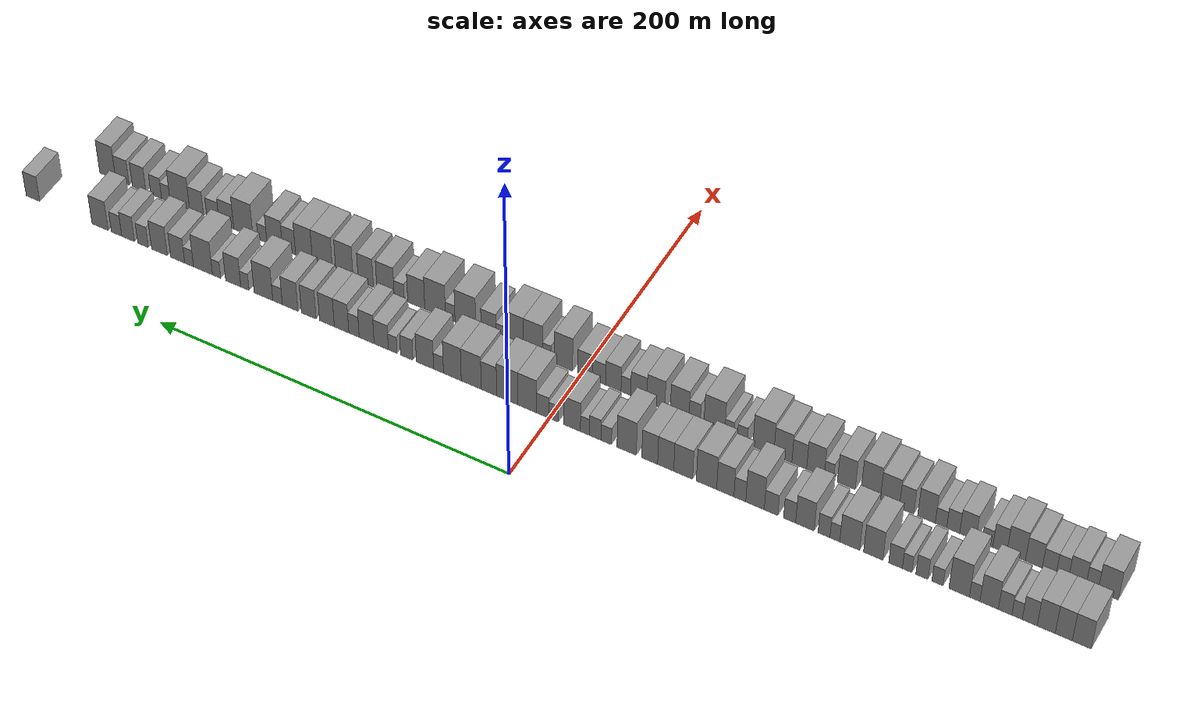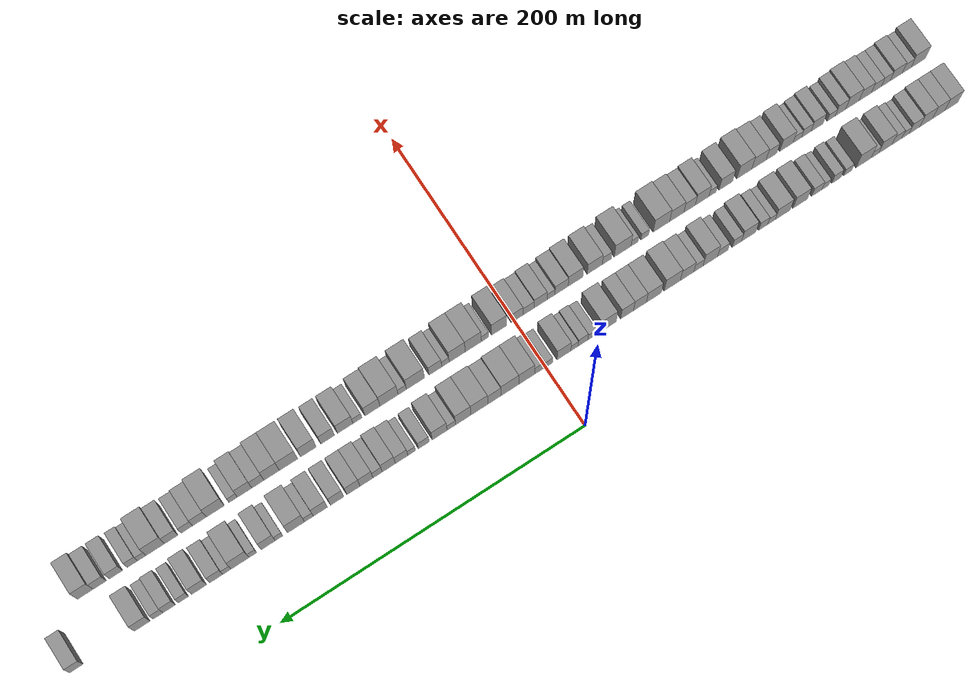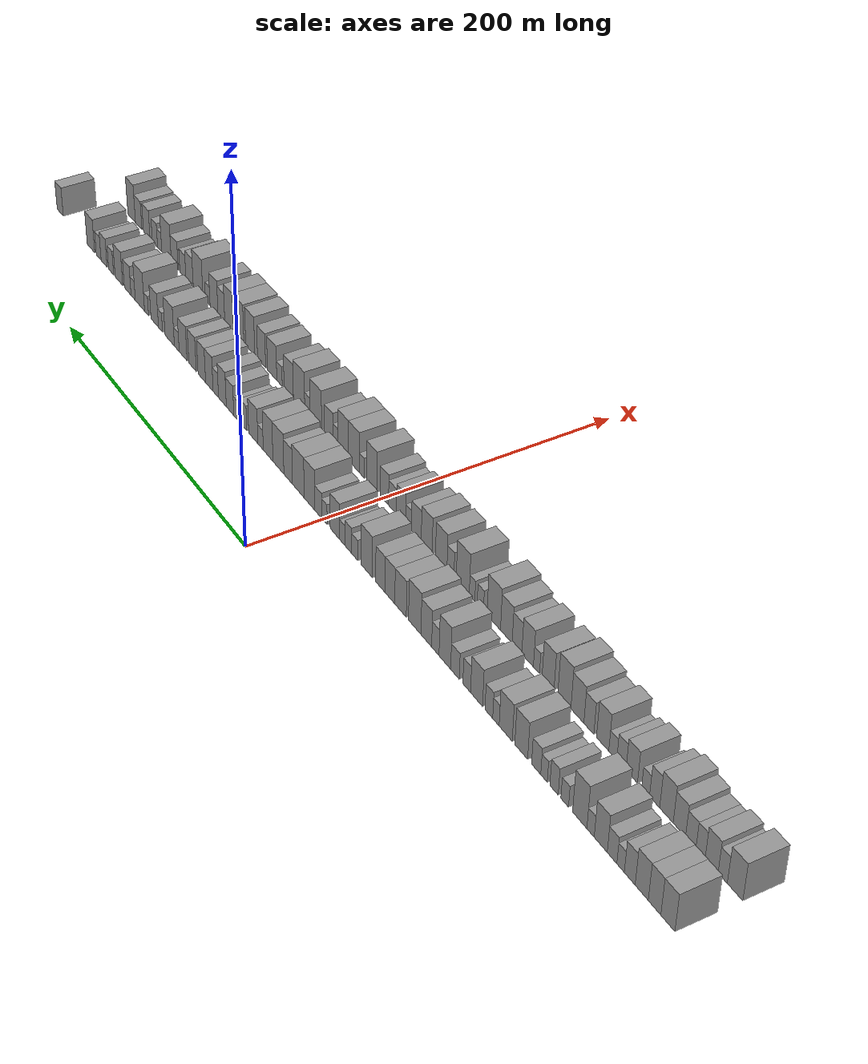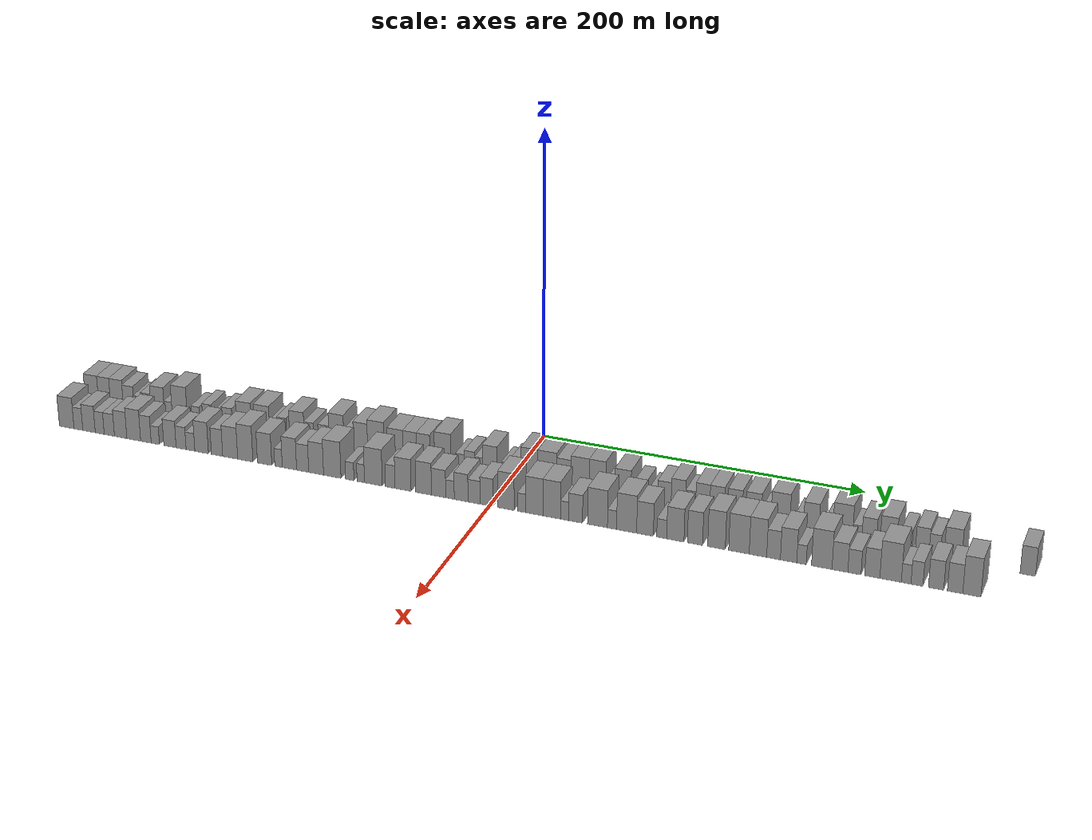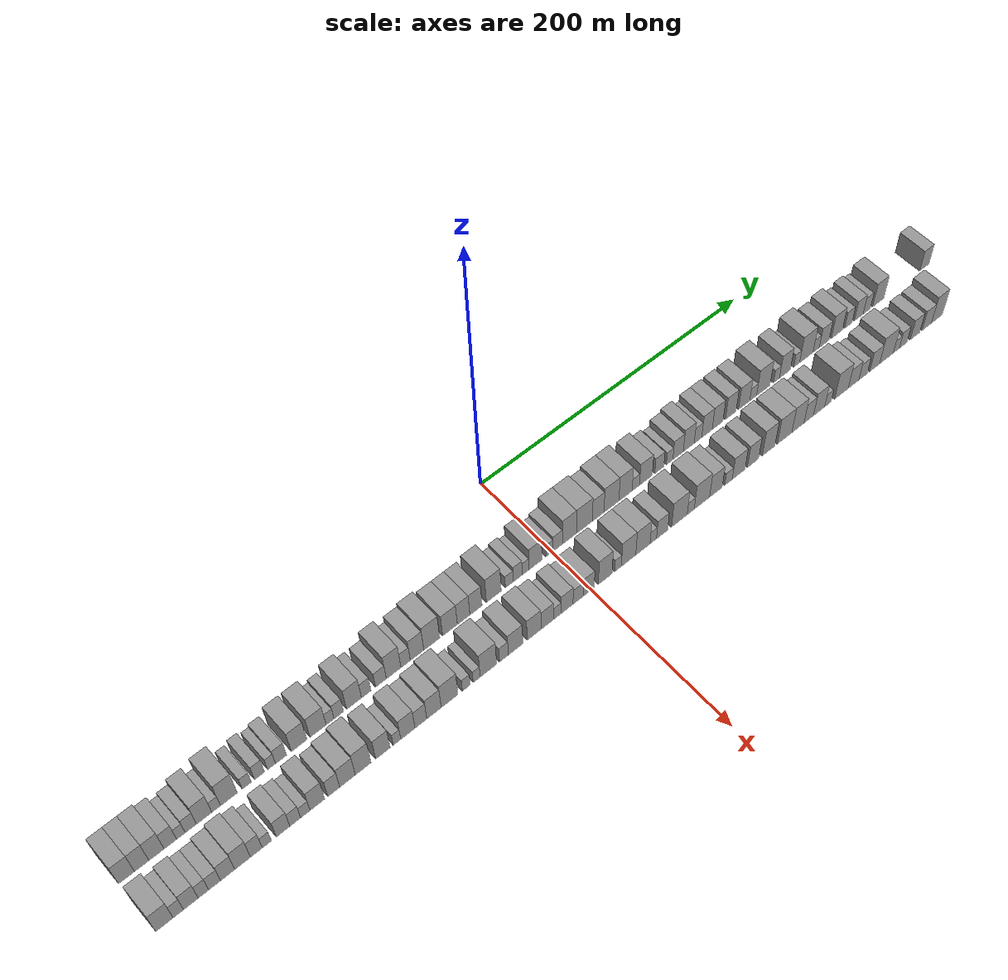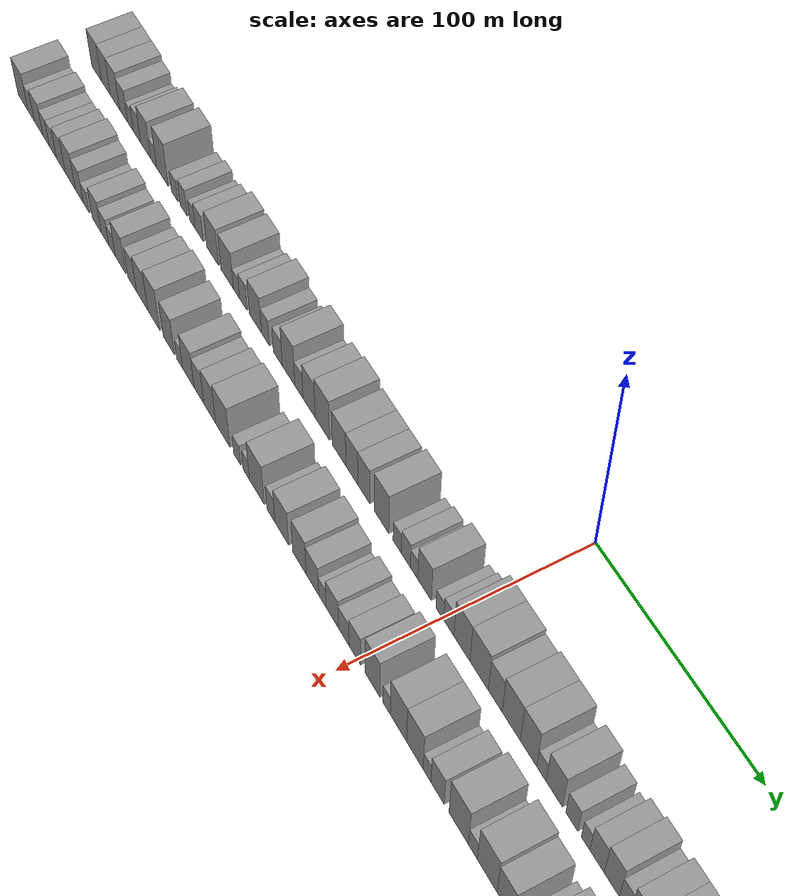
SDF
<sdf version="1.6">
 <world name="default">
  <scene>
   <sky><clouds><speed>12</speed></clouds></sky>
   <ambient>0.4 0.4 0.4 1</ambient>
   <background>0.7 0.7 0.7 1</background>
   <shadows>1</shadows>
  </scene>
  <gravity>0 0 -9.8066</gravity>
  <magnetic_field>6e-06 2.3e-05 -4.2e-05</magnetic_field>
  <physics default="0" name="default_physics" type="ode">
   <ode>
    <solver>
     <type>quick</type>
     <iters>10</iters>
     <sor>1.0</sor>
     <use_dynamic_moi_rescaling>0</use_dynamic_moi_rescaling>
    </solver>
    <constraints>
     <cfm>0</cfm>
     <erp>0.2</erp>
     <contact_max_correcting_vel>100</contact_max_correcting_vel>
     <contact_surface_layer>0.001</contact_surface_layer>
    </constraints>
   </ode>
   <max_step_size>0.004</max_step_size>
   <real_time_factor>1</real_time_factor>
   <real_time_update_rate>250</real_time_update_rate>
  </physics>
  <light name="sun" type="directional">
   <pose>0 0 10 0 0 0</pose>
   <diffuse>0.8 0.8 0.8 1</diffuse>
   <specular>0.2 0.2 0.2 1</specular>
   <attenuation>
    <range>1000</range>
    <constant>0.9</constant>
    <linear>0.01</linear>
    <quadratic>0.001</quadratic>
   </attenuation>
   <direction>-0.5 0.1 -0.9</direction>
  </light>
  <model name="building_1">
   <static>1</static>
   <pose>50.0000 -279.2888 0 0.000000 0.000000 0.000000</pose>
   <link name="link">
    <pose>0 0 10.50 0 0 0</pose>
    <collision name="collision"><geometry><box><size>20.0000 9.4225 21.0000</size></box></geometry></collision>
    <visual name="visual">
     <cast_shadows>0</cast_shadows>
     <geometry><box><size>20.0000 9.4225 21.0000</size></box></geometry>
     <material>
      <script>
       <uri>model://grey_wall/materials/scripts</uri>
       <uri>model://grey_wall/materials/textures</uri>
       <name>vrc/grey_wall</name>
      </script>
     </material>
    </visual>
   </link>
  </model>
  <model name="building_2">
   <static>1</static>
   <pose>50.0000 -270.3135 0 0.000000 0.000000 0.000000</pose>
   <link name="link">
    <pose>0 0 10.50 0 0 0</pose>
    <collision name="collision"><geometry><box><size>20.0000 8.5280 21.0000</size></box></geometry></collision>
    <visual name="visual">
     <cast_shadows>0</cast_shadows>
     <geometry><box><size>20.0000 8.5280 21.0000</size></box></geometry>
     <material>
      <script>
       <uri>model://grey_wall/materials/scripts</uri>
       <uri>model://grey_wall/materials/textures</uri>
       <name>vrc/grey_wall</name>
      </script>
     </material>
    </visual>
   </link>
  </model>
  <model name="building_3">
   <static>1</static>
   <pose>50.0000 -261.5503 0 0.000000 0.000000 0.000000</pose>
   <link name="link">
    <pose>0 0 10.50 0 0 0</pose>
    <collision name="collision"><geometry><box><size>20.0000 8.9983 21.0000</size></box></geometry></collision>
    <visual name="visual">
     <cast_shadows>0</cast_shadows>
     <geometry><box><size>20.0000 8.9983 21.0000</size></box></geometry>
     <material>
      <script>
       <uri>model://grey_wall/materials/scripts</uri>
       <uri>model://grey_wall/materials/textures</uri>
       <name>vrc/grey_wall</name>
      </script>
     </material>
    </visual>
   </link>
  </model>
  <model name="building_4">
   <static>1</static>
   <pose>50.0000 -253.2903 0 0.000000 0.000000 0.000000</pose>
   <link name="link">
    <pose>0 0 9.00 0 0 0</pose>
    <collision name="collision"><geometry><box><size>20.0000 7.5218 18.0000</size></box></geometry></collision>
    <visual name="visual">
     <cast_shadows>0</cast_shadows>
     <geometry><box><size>20.0000 7.5218 18.0000</size></box></geometry>
     <material>
      <script>
       <uri>model://grey_wall/materials/scripts</uri>
       <uri>model://grey_wall/materials/textures</uri>
       <name>vrc/grey_wall</name>
      </script>
     </material>
    </visual>
   </link>
  </model>
  <model name="building_5">
   <static>1</static>
   <pose>50.0000 -246.9302 0 0.000000 0.000000 0.000000</pose>
   <link name="link">
    <pose>0 0 6.00 0 0 0</pose>
    <collision name="collision"><geometry><box><size>20.0000 5.1983 12.0000</size></box></geometry></collision>
    <visual name="visual">
     <cast_shadows>0</cast_shadows>
     <geometry><box><size>20.0000 5.1983 12.0000</size></box></geometry>
     <material>
      <script>
       <uri>model://grey_wall/materials/scripts</uri>
       <uri>model://grey_wall/materials/textures</uri>
       <name>vrc/grey_wall</name>
      </script>
     </material>
    </visual>
   </link>
  </model>
  <model name="building_6">
   <static>1</static>
   <pose>50.0000 -240.9250 0 0.000000 0.000000 0.000000</pose>
   <link name="link">
    <pose>0 0 7.50 0 0 0</pose>
    <collision name="collision"><geometry><box><size>20.0000 6.8121 15.0000</size></box></geometry></collision>
    <visual name="visual">
     <cast_shadows>0</cast_shadows>
     <geometry><box><size>20.0000 6.8121 15.0000</size></box></geometry>
     <material>
      <script>
       <uri>model://grey_wall/materials/scripts</uri>
       <uri>model://grey_wall/materials/textures</uri>
       <name>vrc/grey_wall</name>
      </script>
     </material>
    </visual>
   </link>
  </model>
  <model name="building_7">
   <static>1</static>
   <pose>50.0000 -232.8600 0 0.000000 0.000000 0.000000</pose>
   <link name="link">
    <pose>0 0 10.50 0 0 0</pose>
    <collision name="collision"><geometry><box><size>20.0000 9.3180 21.0000</size></box></geometry></collision>
    <visual name="visual">
     <cast_shadows>0</cast_shadows>
     <geometry><box><size>20.0000 9.3180 21.0000</size></box></geometry>
     <material>
      <script>
       <uri>model://grey_wall/materials/scripts</uri>
       <uri>model://grey_wall/materials/textures</uri>
       <name>vrc/grey_wall</name>
      </script>
     </material>
    </visual>
   </link>
  </model>
  <model name="building_8">
   <static>1</static>
   <pose>50.0000 -225.5299 0 0.000000 0.000000 0.000000</pose>
   <link name="link">
    <pose>0 0 6.00 0 0 0</pose>
    <collision name="collision"><geometry><box><size>20.0000 5.3421 12.0000</size></box></geometry></collision>
    <visual name="visual">
     <cast_shadows>0</cast_shadows>
     <geometry><box><size>20.0000 5.3421 12.0000</size></box></geometry>
     <material>
      <script>
       <uri>model://grey_wall/materials/scripts</uri>
       <uri>model://grey_wall/materials/textures</uri>
       <name>vrc/grey_wall</name>
      </script>
     </material>
    </visual>
   </link>
  </model>
  <model name="building_9">
   <static>1</static>
   <pose>50.0000 -217.6387 0 0.000000 0.000000 0.000000</pose>
   <link name="link">
    <pose>0 0 12.00 0 0 0</pose>
    <collision name="collision"><geometry><box><size>20.0000 10.4403 24.0000</size></box></geometry></collision>
    <visual name="visual">
     <cast_shadows>0</cast_shadows>
     <geometry><box><size>20.0000 10.4403 24.0000</size></box></geometry>
     <material>
      <script>
       <uri>model://grey_wall/materials/scripts</uri>
       <uri>model://grey_wall/materials/textures</uri>
       <name>vrc/grey_wall</name>
      </script>
     </material>
    </visual>
   </link>
  </model>
  <model name="building_10">
   <static>1</static>
   <pose>50.0000 -206.5771 0 0.000000 0.000000 0.000000</pose>
   <link name="link">
    <pose>0 0 6.00 0 0 0</pose>
    <collision name="collision"><geometry><box><size>20.0000 5.6830 12.0000</size></box></geometry></collision>
    <visual name="visual">
     <cast_shadows>0</cast_shadows>
     <geometry><box><size>20.0000 5.6830 12.0000</size></box></geometry>
     <material>
      <script>
       <uri>model://grey_wall/materials/scripts</uri>
       <uri>model://grey_wall/materials/textures</uri>
       <name>vrc/grey_wall</name>
      </script>
     </material>
    </visual>
   </link>
  </model>
  <model name="building_11">
   <static>1</static>
   <pose>50.0000 -198.6190 0 0.000000 0.000000 0.000000</pose>
   <link name="link">
    <pose>0 0 7.50 0 0 0</pose>
    <collision name="collision"><geometry><box><size>20.0000 6.2331 15.0000</size></box></geometry></collision>
    <visual name="visual">
     <cast_shadows>0</cast_shadows>
     <geometry><box><size>20.0000 6.2331 15.0000</size></box></geometry>
     <material>
      <script>
       <uri>model://grey_wall/materials/scripts</uri>
       <uri>model://grey_wall/materials/textures</uri>
       <name>vrc/grey_wall</name>
      </script>
     </material>
    </visual>
   </link>
  </model>
  <model name="building_12">
   <static>1</static>
   <pose>50.0000 -191.0280 0 0.000000 0.000000 0.000000</pose>
   <link name="link">
    <pose>0 0 6.00 0 0 0</pose>
    <collision name="collision"><geometry><box><size>20.0000 4.9491 12.0000</size></box></geometry></collision>
    <visual name="visual">
     <cast_shadows>0</cast_shadows>
     <geometry><box><size>20.0000 4.9491 12.0000</size></box></geometry>
     <material>
      <script>
       <uri>model://grey_wall/materials/scripts</uri>
       <uri>model://grey_wall/materials/textures</uri>
       <name>vrc/grey_wall</name>
      </script>
     </material>
    </visual>
   </link>
  </model>
  <model name="building_13">
   <static>1</static>
   <pose>50.0000 -185.0274 0 0.000000 0.000000 0.000000</pose>
   <link name="link">
    <pose>0 0 7.50 0 0 0</pose>
    <collision name="collision"><geometry><box><size>20.0000 7.0521 15.0000</size></box></geometry></collision>
    <visual name="visual">
     <cast_shadows>0</cast_shadows>
     <geometry><box><size>20.0000 7.0521 15.0000</size></box></geometry>
     <material>
      <script>
       <uri>model://grey_wall/materials/scripts</uri>
       <uri>model://grey_wall/materials/textures</uri>
       <name>vrc/grey_wall</name>
      </script>
     </material>
    </visual>
   </link>
  </model>
  <model name="building_14">
   <static>1</static>
   <pose>50.0000 -173.4925 0 0.000000 0.000000 0.000000</pose>
   <link name="link">
    <pose>0 0 10.50 0 0 0</pose>
    <collision name="collision"><geometry><box><size>20.0000 10.0176 21.0000</size></box></geometry></collision>
    <visual name="visual">
     <cast_shadows>0</cast_shadows>
     <geometry><box><size>20.0000 10.0176 21.0000</size></box></geometry>
     <material>
      <script>
       <uri>model://grey_wall/materials/scripts</uri>
       <uri>model://grey_wall/materials/textures</uri>
       <name>vrc/grey_wall</name>
      </script>
     </material>
    </visual>
   </link>
  </model>
  <model name="building_15">
   <static>1</static>
   <pose>50.0000 -161.2833 0 0.000000 0.000000 0.000000</pose>
   <link name="link">
    <pose>0 0 10.50 0 0 0</pose>
    <collision name="collision"><geometry><box><size>20.0000 10.4008 21.0000</size></box></geometry></collision>
    <visual name="visual">
     <cast_shadows>0</cast_shadows>
     <geometry><box><size>20.0000 10.4008 21.0000</size></box></geometry>
     <material>
      <script>
       <uri>model://grey_wall/materials/scripts</uri>
       <uri>model://grey_wall/materials/textures</uri>
       <name>vrc/grey_wall</name>
      </script>
     </material>
    </visual>
   </link>
  </model>
  <model name="building_16">
   <static>1</static>
   <pose>50.0000 -153.5097 0 0.000000 0.000000 0.000000</pose>
   <link name="link">
    <pose>0 0 6.00 0 0 0</pose>
    <collision name="collision"><geometry><box><size>20.0000 5.1463 12.0000</size></box></geometry></collision>
    <visual name="visual">
     <cast_shadows>0</cast_shadows>
     <geometry><box><size>20.0000 5.1463 12.0000</size></box></geometry>
     <material>
      <script>
       <uri>model://grey_wall/materials/scripts</uri>
       <uri>model://grey_wall/materials/textures</uri>
       <name>vrc/grey_wall</name>
      </script>
     </material>
    </visual>
   </link>
  </model>
  <model name="building_17">
   <static>1</static>
   <pose>50.0000 -147.8316 0 0.000000 0.000000 0.000000</pose>
   <link name="link">
    <pose>0 0 7.50 0 0 0</pose>
    <collision name="collision"><geometry><box><size>20.0000 6.2099 15.0000</size></box></geometry></collision>
    <visual name="visual">
     <cast_shadows>0</cast_shadows>
     <geometry><box><size>20.0000 6.2099 15.0000</size></box></geometry>
     <material>
      <script>
       <uri>model://grey_wall/materials/scripts</uri>
       <uri>model://grey_wall/materials/textures</uri>
       <name>vrc/grey_wall</name>
      </script>
     </material>
    </visual>
   </link>
  </model>
  <model name="building_18">
   <static>1</static>
   <pose>50.0000 -137.8223 0 0.000000 0.000000 0.000000</pose>
   <link name="link">
    <pose>0 0 10.50 0 0 0</pose>
    <collision name="collision"><geometry><box><size>20.0000 9.8088 21.0000</size></box></geometry></collision>
    <visual name="visual">
     <cast_shadows>0</cast_shadows>
     <geometry><box><size>20.0000 9.8088 21.0000</size></box></geometry>
     <material>
      <script>
       <uri>model://grey_wall/materials/scripts</uri>
       <uri>model://grey_wall/materials/textures</uri>
       <name>vrc/grey_wall</name>
      </script>
     </material>
    </visual>
   </link>
  </model>
  <model name="building_19">
   <static>1</static>
   <pose>50.0000 -129.7433 0 0.000000 0.000000 0.000000</pose>
   <link name="link">
    <pose>0 0 7.50 0 0 0</pose>
    <collision name="collision"><geometry><box><size>20.0000 6.3491 15.0000</size></box></geometry></collision>
    <visual name="visual">
     <cast_shadows>0</cast_shadows>
     <geometry><box><size>20.0000 6.3491 15.0000</size></box></geometry>
     <material>
      <script>
       <uri>model://grey_wall/materials/scripts</uri>
       <uri>model://grey_wall/materials/textures</uri>
       <name>vrc/grey_wall</name>
      </script>
     </material>
    </visual>
   </link>
  </model>
  <model name="building_20">
   <static>1</static>
   <pose>50.0000 -119.9669 0 0.000000 0.000000 0.000000</pose>
   <link name="link">
    <pose>0 0 7.50 0 0 0</pose>
    <collision name="collision"><geometry><box><size>20.0000 7.2037 15.0000</size></box></geometry></collision>
    <visual name="visual">
     <cast_shadows>0</cast_shadows>
     <geometry><box><size>20.0000 7.2037 15.0000</size></box></geometry>
     <material>
      <script>
       <uri>model://grey_wall/materials/scripts</uri>
       <uri>model://grey_wall/materials/textures</uri>
       <name>vrc/grey_wall</name>
      </script>
     </material>
    </visual>
   </link>
  </model>
  <model name="building_21">
   <static>1</static>
   <pose>50.0000 -111.4298 0 0.000000 0.000000 0.000000</pose>
   <link name="link">
    <pose>0 0 12.00 0 0 0</pose>
    <collision name="collision"><geometry><box><size>20.0000 9.8705 24.0000</size></box></geometry></collision>
    <visual name="visual">
     <cast_shadows>0</cast_shadows>
     <geometry><box><size>20.0000 9.8705 24.0000</size></box></geometry>
     <material>
      <script>
       <uri>model://grey_wall/materials/scripts</uri>
       <uri>model://grey_wall/materials/textures</uri>
       <name>vrc/grey_wall</name>
      </script>
     </material>
    </visual>
   </link>
  </model>
  <model name="building_22">
   <static>1</static>
   <pose>50.0000 -103.3395 0 0.000000 0.000000 0.000000</pose>
   <link name="link">
    <pose>0 0 7.50 0 0 0</pose>
    <collision name="collision"><geometry><box><size>20.0000 6.3101 15.0000</size></box></geometry></collision>
    <visual name="visual">
     <cast_shadows>0</cast_shadows>
     <geometry><box><size>20.0000 6.3101 15.0000</size></box></geometry>
     <material>
      <script>
       <uri>model://grey_wall/materials/scripts</uri>
       <uri>model://grey_wall/materials/textures</uri>
       <name>vrc/grey_wall</name>
      </script>
     </material>
    </visual>
   </link>
  </model>
  <model name="building_23">
   <static>1</static>
   <pose>50.0000 -95.5627 0 0.000000 0.000000 0.000000</pose>
   <link name="link">
    <pose>0 0 10.50 0 0 0</pose>
    <collision name="collision"><geometry><box><size>20.0000 9.2436 21.0000</size></box></geometry></collision>
    <visual name="visual">
     <cast_shadows>0</cast_shadows>
     <geometry><box><size>20.0000 9.2436 21.0000</size></box></geometry>
     <material>
      <script>
       <uri>model://grey_wall/materials/scripts</uri>
       <uri>model://grey_wall/materials/textures</uri>
       <name>vrc/grey_wall</name>
      </script>
     </material>
    </visual>
   </link>
  </model>
  <model name="building_24">
   <static>1</static>
   <pose>50.0000 -85.4718 0 0.000000 0.000000 0.000000</pose>
   <link name="link">
    <pose>0 0 12.00 0 0 0</pose>
    <collision name="collision"><geometry><box><size>20.0000 10.9383 24.0000</size></box></geometry></collision>
    <visual name="visual">
     <cast_shadows>0</cast_shadows>
     <geometry><box><size>20.0000 10.9383 24.0000</size></box></geometry>
     <material>
      <script>
       <uri>model://grey_wall/materials/scripts</uri>
       <uri>model://grey_wall/materials/textures</uri>
       <name>vrc/grey_wall</name>
      </script>
     </material>
    </visual>
   </link>
  </model>
  <model name="building_25">
   <static>1</static>
   <pose>50.0000 -72.9098 0 0.000000 0.000000 0.000000</pose>
   <link name="link">
    <pose>0 0 10.50 0 0 0</pose>
    <collision name="collision"><geometry><box><size>20.0000 10.1855 21.0000</size></box></geometry></collision>
    <visual name="visual">
     <cast_shadows>0</cast_shadows>
     <geometry><box><size>20.0000 10.1855 21.0000</size></box></geometry>
     <material>
      <script>
       <uri>model://grey_wall/materials/scripts</uri>
       <uri>model://grey_wall/materials/textures</uri>
       <name>vrc/grey_wall</name>
      </script>
     </material>
    </visual>
   </link>
  </model>
  <model name="building_26">
   <static>1</static>
   <pose>50.0000 -63.4511 0 0.000000 0.000000 0.000000</pose>
   <link name="link">
    <pose>0 0 10.50 0 0 0</pose>
    <collision name="collision"><geometry><box><size>20.0000 8.7318 21.0000</size></box></geometry></collision>
    <visual name="visual">
     <cast_shadows>0</cast_shadows>
     <geometry><box><size>20.0000 8.7318 21.0000</size></box></geometry>
     <material>
      <script>
       <uri>model://grey_wall/materials/scripts</uri>
       <uri>model://grey_wall/materials/textures</uri>
       <name>vrc/grey_wall</name>
      </script>
     </material>
    </visual>
   </link>
  </model>
  <model name="building_27">
   <static>1</static>
   <pose>50.0000 -54.7718 0 0.000000 0.000000 0.000000</pose>
   <link name="link">
    <pose>0 0 10.50 0 0 0</pose>
    <collision name="collision"><geometry><box><size>20.0000 8.6268 21.0000</size></box></geometry></collision>
    <visual name="visual">
     <cast_shadows>0</cast_shadows>
     <geometry><box><size>20.0000 8.6268 21.0000</size></box></geometry>
     <material>
      <script>
       <uri>model://grey_wall/materials/scripts</uri>
       <uri>model://grey_wall/materials/textures</uri>
       <name>vrc/grey_wall</name>
      </script>
     </material>
    </visual>
   </link>
  </model>
  <model name="building_28">
   <static>1</static>
   <pose>50.0000 -42.1871 0 0.000000 0.000000 0.000000</pose>
   <link name="link">
    <pose>0 0 12.00 0 0 0</pose>
    <collision name="collision"><geometry><box><size>20.0000 10.5426 24.0000</size></box></geometry></collision>
    <visual name="visual">
     <cast_shadows>0</cast_shadows>
     <geometry><box><size>20.0000 10.5426 24.0000</size></box></geometry>
     <material>
      <script>
       <uri>model://grey_wall/materials/scripts</uri>
       <uri>model://grey_wall/materials/textures</uri>
       <name>vrc/grey_wall</name>
      </script>
     </material>
    </visual>
   </link>
  </model>
  <model name="building_29">
   <static>1</static>
   <pose>50.0000 -31.0601 0 0.000000 0.000000 0.000000</pose>
   <link name="link">
    <pose>0 0 6.00 0 0 0</pose>
    <collision name="collision"><geometry><box><size>20.0000 5.7115 12.0000</size></box></geometry></collision>
    <visual name="visual">
     <cast_shadows>0</cast_shadows>
     <geometry><box><size>20.0000 5.7115 12.0000</size></box></geometry>
     <material>
      <script>
       <uri>model://grey_wall/materials/scripts</uri>
       <uri>model://grey_wall/materials/textures</uri>
       <name>vrc/grey_wall</name>
      </script>
     </material>
    </visual>
   </link>
  </model>
  <model name="building_30">
   <static>1</static>
   <pose>50.0000 -24.9996 0 0.000000 0.000000 0.000000</pose>
   <link name="link">
    <pose>0 0 7.50 0 0 0</pose>
    <collision name="collision"><geometry><box><size>20.0000 6.4095 15.0000</size></box></geometry></collision>
    <visual name="visual">
     <cast_shadows>0</cast_shadows>
     <geometry><box><size>20.0000 6.4095 15.0000</size></box></geometry>
     <material>
      <script>
       <uri>model://grey_wall/materials/scripts</uri>
       <uri>model://grey_wall/materials/textures</uri>
       <name>vrc/grey_wall</name>
      </script>
     </material>
    </visual>
   </link>
  </model>
  <model name="building_31">
   <static>1</static>
   <pose>50.0000 -19.2891 0 0.000000 0.000000 0.000000</pose>
   <link name="link">
    <pose>0 0 6.00 0 0 0</pose>
    <collision name="collision"><geometry><box><size>20.0000 5.0114 12.0000</size></box></geometry></collision>
    <visual name="visual">
     <cast_shadows>0</cast_shadows>
     <geometry><box><size>20.0000 5.0114 12.0000</size></box></geometry>
     <material>
      <script>
       <uri>model://grey_wall/materials/scripts</uri>
       <uri>model://grey_wall/materials/textures</uri>
       <name>vrc/grey_wall</name>
      </script>
     </material>
    </visual>
   </link>
  </model>
  <model name="building_32">
   <static>1</static>
   <pose>50.0000 -12.1653 0 0.000000 0.000000 0.000000</pose>
   <link name="link">
    <pose>0 0 10.50 0 0 0</pose>
    <collision name="collision"><geometry><box><size>20.0000 9.2364 21.0000</size></box></geometry></collision>
    <visual name="visual">
     <cast_shadows>0</cast_shadows>
     <geometry><box><size>20.0000 9.2364 21.0000</size></box></geometry>
     <material>
      <script>
       <uri>model://grey_wall/materials/scripts</uri>
       <uri>model://grey_wall/materials/textures</uri>
       <name>vrc/grey_wall</name>
      </script>
     </material>
    </visual>
   </link>
  </model>
  <model name="building_33">
   <static>1</static>
   <pose>50.0000 -1.9097 0 0.000000 0.000000 0.000000</pose>
   <link name="link">
    <pose>0 0 6.00 0 0 0</pose>
    <collision name="collision"><geometry><box><size>20.0000 5.2747 12.0000</size></box></geometry></collision>
    <visual name="visual">
     <cast_shadows>0</cast_shadows>
     <geometry><box><size>20.0000 5.2747 12.0000</size></box></geometry>
     <material>
      <script>
       <uri>model://grey_wall/materials/scripts</uri>
       <uri>model://grey_wall/materials/textures</uri>
       <name>vrc/grey_wall</name>
      </script>
     </material>
    </visual>
   </link>
  </model>
  <model name="building_34">
   <static>1</static>
   <pose>50.0000 4.1421 0 0.000000 0.000000 0.000000</pose>
   <link name="link">
    <pose>0 0 7.50 0 0 0</pose>
    <collision name="collision"><geometry><box><size>20.0000 6.8289 15.0000</size></box></geometry></collision>
    <visual name="visual">
     <cast_shadows>0</cast_shadows>
     <geometry><box><size>20.0000 6.8289 15.0000</size></box></geometry>
     <material>
      <script>
       <uri>model://grey_wall/materials/scripts</uri>
       <uri>model://grey_wall/materials/textures</uri>
       <name>vrc/grey_wall</name>
      </script>
     </material>
    </visual>
   </link>
  </model>
  <model name="building_35">
   <static>1</static>
   <pose>50.0000 12.7904 0 0.000000 0.000000 0.000000</pose>
   <link name="link">
    <pose>0 0 12.00 0 0 0</pose>
    <collision name="collision"><geometry><box><size>20.0000 10.4679 24.0000</size></box></geometry></collision>
    <visual name="visual">
     <cast_shadows>0</cast_shadows>
     <geometry><box><size>20.0000 10.4679 24.0000</size></box></geometry>
     <material>
      <script>
       <uri>model://grey_wall/materials/scripts</uri>
       <uri>model://grey_wall/materials/textures</uri>
       <name>vrc/grey_wall</name>
      </script>
     </material>
    </visual>
   </link>
  </model>
  <model name="building_36">
   <static>1</static>
   <pose>50.0000 23.9557 0 0.000000 0.000000 0.000000</pose>
   <link name="link">
    <pose>0 0 12.00 0 0 0</pose>
    <collision name="collision"><geometry><box><size>20.0000 11.8626 24.0000</size></box></geometry></collision>
    <visual name="visual">
     <cast_shadows>0</cast_shadows>
     <geometry><box><size>20.0000 11.8626 24.0000</size></box></geometry>
     <material>
      <script>
       <uri>model://grey_wall/materials/scripts</uri>
       <uri>model://grey_wall/materials/textures</uri>
       <name>vrc/grey_wall</name>
      </script>
     </material>
    </visual>
   </link>
  </model>
  <model name="building_37">
   <static>1</static>
   <pose>50.0000 34.2631 0 0.000000 0.000000 0.000000</pose>
   <link name="link">
    <pose>0 0 10.50 0 0 0</pose>
    <collision name="collision"><geometry><box><size>20.0000 8.7522 21.0000</size></box></geometry></collision>
    <visual name="visual">
     <cast_shadows>0</cast_shadows>
     <geometry><box><size>20.0000 8.7522 21.0000</size></box></geometry>
     <material>
      <script>
       <uri>model://grey_wall/materials/scripts</uri>
       <uri>model://grey_wall/materials/textures</uri>
       <name>vrc/grey_wall</name>
      </script>
     </material>
    </visual>
   </link>
  </model>
  <model name="building_38">
   <static>1</static>
   <pose>50.0000 44.2862 0 0.000000 0.000000 0.000000</pose>
   <link name="link">
    <pose>0 0 12.00 0 0 0</pose>
    <collision name="collision"><geometry><box><size>20.0000 11.2942 24.0000</size></box></geometry></collision>
    <visual name="visual">
     <cast_shadows>0</cast_shadows>
     <geometry><box><size>20.0000 11.2942 24.0000</size></box></geometry>
     <material>
      <script>
       <uri>model://grey_wall/materials/scripts</uri>
       <uri>model://grey_wall/materials/textures</uri>
       <name>vrc/grey_wall</name>
      </script>
     </material>
    </visual>
   </link>
  </model>
  <model name="building_39">
   <static>1</static>
   <pose>50.0000 54.9915 0 0.000000 0.000000 0.000000</pose>
   <link name="link">
    <pose>0 0 12.00 0 0 0</pose>
    <collision name="collision"><geometry><box><size>20.0000 10.1165 24.0000</size></box></geometry></collision>
    <visual name="visual">
     <cast_shadows>0</cast_shadows>
     <geometry><box><size>20.0000 10.1165 24.0000</size></box></geometry>
     <material>
      <script>
       <uri>model://grey_wall/materials/scripts</uri>
       <uri>model://grey_wall/materials/textures</uri>
       <name>vrc/grey_wall</name>
      </script>
     </material>
    </visual>
   </link>
  </model>
  <model name="building_40">
   <static>1</static>
   <pose>50.0000 62.8666 0 0.000000 0.000000 0.000000</pose>
   <link name="link">
    <pose>0 0 6.00 0 0 0</pose>
    <collision name="collision"><geometry><box><size>20.0000 5.6337 12.0000</size></box></geometry></collision>
    <visual name="visual">
     <cast_shadows>0</cast_shadows>
     <geometry><box><size>20.0000 5.6337 12.0000</size></box></geometry>
     <material>
      <script>
       <uri>model://grey_wall/materials/scripts</uri>
       <uri>model://grey_wall/materials/textures</uri>
       <name>vrc/grey_wall</name>
      </script>
     </material>
    </visual>
   </link>
  </model>
  <model name="building_41">
   <static>1</static>
   <pose>50.0000 70.6148 0 0.000000 0.000000 0.000000</pose>
   <link name="link">
    <pose>0 0 10.50 0 0 0</pose>
    <collision name="collision"><geometry><box><size>20.0000 9.8627 21.0000</size></box></geometry></collision>
    <visual name="visual">
     <cast_shadows>0</cast_shadows>
     <geometry><box><size>20.0000 9.8627 21.0000</size></box></geometry>
     <material>
      <script>
       <uri>model://grey_wall/materials/scripts</uri>
       <uri>model://grey_wall/materials/textures</uri>
       <name>vrc/grey_wall</name>
      </script>
     </material>
    </visual>
   </link>
  </model>
  <model name="building_42">
   <static>1</static>
   <pose>50.0000 81.0959 0 0.000000 0.000000 0.000000</pose>
   <link name="link">
    <pose>0 0 7.50 0 0 0</pose>
    <collision name="collision"><geometry><box><size>20.0000 7.0994 15.0000</size></box></geometry></collision>
    <visual name="visual">
     <cast_shadows>0</cast_shadows>
     <geometry><box><size>20.0000 7.0994 15.0000</size></box></geometry>
     <material>
      <script>
       <uri>model://grey_wall/materials/scripts</uri>
       <uri>model://grey_wall/materials/textures</uri>
       <name>vrc/grey_wall</name>
      </script>
     </material>
    </visual>
   </link>
  </model>
  <model name="building_43">
   <static>1</static>
   <pose>50.0000 89.1589 0 0.000000 0.000000 0.000000</pose>
   <link name="link">
    <pose>0 0 6.00 0 0 0</pose>
    <collision name="collision"><geometry><box><size>20.0000 5.0266 12.0000</size></box></geometry></collision>
    <visual name="visual">
     <cast_shadows>0</cast_shadows>
     <geometry><box><size>20.0000 5.0266 12.0000</size></box></geometry>
     <material>
      <script>
       <uri>model://grey_wall/materials/scripts</uri>
       <uri>model://grey_wall/materials/textures</uri>
       <name>vrc/grey_wall</name>
      </script>
     </material>
    </visual>
   </link>
  </model>
  <model name="building_44">
   <static>1</static>
   <pose>50.0000 95.7803 0 0.000000 0.000000 0.000000</pose>
   <link name="link">
    <pose>0 0 9.00 0 0 0</pose>
    <collision name="collision"><geometry><box><size>20.0000 8.2162 18.0000</size></box></geometry></collision>
    <visual name="visual">
     <cast_shadows>0</cast_shadows>
     <geometry><box><size>20.0000 8.2162 18.0000</size></box></geometry>
     <material>
      <script>
       <uri>model://grey_wall/materials/scripts</uri>
       <uri>model://grey_wall/materials/textures</uri>
       <name>vrc/grey_wall</name>
      </script>
     </material>
    </visual>
   </link>
  </model>
  <model name="building_45">
   <static>1</static>
   <pose>50.0000 104.2209 0 0.000000 0.000000 0.000000</pose>
   <link name="link">
    <pose>0 0 10.50 0 0 0</pose>
    <collision name="collision"><geometry><box><size>20.0000 8.6650 21.0000</size></box></geometry></collision>
    <visual name="visual">
     <cast_shadows>0</cast_shadows>
     <geometry><box><size>20.0000 8.6650 21.0000</size></box></geometry>
     <material>
      <script>
       <uri>model://grey_wall/materials/scripts</uri>
       <uri>model://grey_wall/materials/textures</uri>
       <name>vrc/grey_wall</name>
      </script>
     </material>
    </visual>
   </link>
  </model>
  <model name="building_46">
   <static>1</static>
   <pose>50.0000 111.5624 0 0.000000 0.000000 0.000000</pose>
   <link name="link">
    <pose>0 0 7.50 0 0 0</pose>
    <collision name="collision"><geometry><box><size>20.0000 6.0179 15.0000</size></box></geometry></collision>
    <visual name="visual">
     <cast_shadows>0</cast_shadows>
     <geometry><box><size>20.0000 6.0179 15.0000</size></box></geometry>
     <material>
      <script>
       <uri>model://grey_wall/materials/scripts</uri>
       <uri>model://grey_wall/materials/textures</uri>
       <name>vrc/grey_wall</name>
      </script>
     </material>
    </visual>
   </link>
  </model>
  <model name="building_47">
   <static>1</static>
   <pose>50.0000 118.7976 0 0.000000 0.000000 0.000000</pose>
   <link name="link">
    <pose>0 0 10.50 0 0 0</pose>
    <collision name="collision"><geometry><box><size>20.0000 8.4525 21.0000</size></box></geometry></collision>
    <visual name="visual">
     <cast_shadows>0</cast_shadows>
     <geometry><box><size>20.0000 8.4525 21.0000</size></box></geometry>
     <material>
      <script>
       <uri>model://grey_wall/materials/scripts</uri>
       <uri>model://grey_wall/materials/textures</uri>
       <name>vrc/grey_wall</name>
      </script>
     </material>
    </visual>
   </link>
  </model>
  <model name="building_48">
   <static>1</static>
   <pose>50.0000 127.3523 0 0.000000 0.000000 0.000000</pose>
   <link name="link">
    <pose>0 0 10.50 0 0 0</pose>
    <collision name="collision"><geometry><box><size>20.0000 8.6569 21.0000</size></box></geometry></collision>
    <visual name="visual">
     <cast_shadows>0</cast_shadows>
     <geometry><box><size>20.0000 8.6569 21.0000</size></box></geometry>
     <material>
      <script>
       <uri>model://grey_wall/materials/scripts</uri>
       <uri>model://grey_wall/materials/textures</uri>
       <name>vrc/grey_wall</name>
      </script>
     </material>
    </visual>
   </link>
  </model>
  <model name="building_49">
   <static>1</static>
   <pose>50.0000 138.0008 0 0.000000 0.000000 0.000000</pose>
   <link name="link">
    <pose>0 0 10.50 0 0 0</pose>
    <collision name="collision"><geometry><box><size>20.0000 8.6401 21.0000</size></box></geometry></collision>
    <visual name="visual">
     <cast_shadows>0</cast_shadows>
     <geometry><box><size>20.0000 8.6401 21.0000</size></box></geometry>
     <material>
      <script>
       <uri>model://grey_wall/materials/scripts</uri>
       <uri>model://grey_wall/materials/textures</uri>
       <name>vrc/grey_wall</name>
      </script>
     </material>
    </visual>
   </link>
  </model>
  <model name="building_50">
   <static>1</static>
   <pose>50.0000 148.9457 0 0.000000 0.000000 0.000000</pose>
   <link name="link">
    <pose>0 0 10.50 0 0 0</pose>
    <collision name="collision"><geometry><box><size>20.0000 9.2497 21.0000</size></box></geometry></collision>
    <visual name="visual">
     <cast_shadows>0</cast_shadows>
     <geometry><box><size>20.0000 9.2497 21.0000</size></box></geometry>
     <material>
      <script>
       <uri>model://grey_wall/materials/scripts</uri>
       <uri>model://grey_wall/materials/textures</uri>
       <name>vrc/grey_wall</name>
      </script>
     </material>
    </visual>
   </link>
  </model>
  <model name="building_51">
   <static>1</static>
   <pose>50.0000 156.3845 0 0.000000 0.000000 0.000000</pose>
   <link name="link">
    <pose>0 0 6.00 0 0 0</pose>
    <collision name="collision"><geometry><box><size>20.0000 5.6278 12.0000</size></box></geometry></collision>
    <visual name="visual">
     <cast_shadows>0</cast_shadows>
     <geometry><box><size>20.0000 5.6278 12.0000</size></box></geometry>
     <material>
      <script>
       <uri>model://grey_wall/materials/scripts</uri>
       <uri>model://grey_wall/materials/textures</uri>
       <name>vrc/grey_wall</name>
      </script>
     </material>
    </visual>
   </link>
  </model>
  <model name="building_52">
   <static>1</static>
   <pose>50.0000 164.7466 0 0.000000 0.000000 0.000000</pose>
   <link name="link">
    <pose>0 0 12.00 0 0 0</pose>
    <collision name="collision"><geometry><box><size>20.0000 11.0963 24.0000</size></box></geometry></collision>
    <visual name="visual">
     <cast_shadows>0</cast_shadows>
     <geometry><box><size>20.0000 11.0963 24.0000</size></box></geometry>
     <material>
      <script>
       <uri>model://grey_wall/materials/scripts</uri>
       <uri>model://grey_wall/materials/textures</uri>
       <name>vrc/grey_wall</name>
      </script>
     </material>
    </visual>
   </link>
  </model>
  <model name="building_53">
   <static>1</static>
   <pose>50.0000 175.7574 0 0.000000 0.000000 0.000000</pose>
   <link name="link">
    <pose>0 0 6.00 0 0 0</pose>
    <collision name="collision"><geometry><box><size>20.0000 4.9253 12.0000</size></box></geometry></collision>
    <visual name="visual">
     <cast_shadows>0</cast_shadows>
     <geometry><box><size>20.0000 4.9253 12.0000</size></box></geometry>
     <material>
      <script>
       <uri>model://grey_wall/materials/scripts</uri>
       <uri>model://grey_wall/materials/textures</uri>
       <name>vrc/grey_wall</name>
      </script>
     </material>
    </visual>
   </link>
  </model>
  <model name="building_54">
   <static>1</static>
   <pose>50.0000 182.7451 0 0.000000 0.000000 0.000000</pose>
   <link name="link">
    <pose>0 0 10.50 0 0 0</pose>
    <collision name="collision"><geometry><box><size>20.0000 9.0500 21.0000</size></box></geometry></collision>
    <visual name="visual">
     <cast_shadows>0</cast_shadows>
     <geometry><box><size>20.0000 9.0500 21.0000</size></box></geometry>
     <material>
      <script>
       <uri>model://grey_wall/materials/scripts</uri>
       <uri>model://grey_wall/materials/textures</uri>
       <name>vrc/grey_wall</name>
      </script>
     </material>
    </visual>
   </link>
  </model>
  <model name="building_55">
   <static>1</static>
   <pose>50.0000 192.7266 0 0.000000 0.000000 0.000000</pose>
   <link name="link">
    <pose>0 0 6.00 0 0 0</pose>
    <collision name="collision"><geometry><box><size>20.0000 4.9130 12.0000</size></box></geometry></collision>
    <visual name="visual">
     <cast_shadows>0</cast_shadows>
     <geometry><box><size>20.0000 4.9130 12.0000</size></box></geometry>
     <material>
      <script>
       <uri>model://grey_wall/materials/scripts</uri>
       <uri>model://grey_wall/materials/textures</uri>
       <name>vrc/grey_wall</name>
      </script>
     </material>
    </visual>
   </link>
  </model>
  <model name="building_56">
   <static>1</static>
   <pose>50.0000 200.9082 0 0.000000 0.000000 0.000000</pose>
   <link name="link">
    <pose>0 0 12.00 0 0 0</pose>
    <collision name="collision"><geometry><box><size>20.0000 11.4501 24.0000</size></box></geometry></collision>
    <visual name="visual">
     <cast_shadows>0</cast_shadows>
     <geometry><box><size>20.0000 11.4501 24.0000</size></box></geometry>
     <material>
      <script>
       <uri>model://grey_wall/materials/scripts</uri>
       <uri>model://grey_wall/materials/textures</uri>
       <name>vrc/grey_wall</name>
      </script>
     </material>
    </visual>
   </link>
  </model>
  <model name="building_57">
   <static>1</static>
   <pose>50.0000 209.3006 0 0.000000 0.000000 0.000000</pose>
   <link name="link">
    <pose>0 0 6.00 0 0 0</pose>
    <collision name="collision"><geometry><box><size>20.0000 5.3347 12.0000</size></box></geometry></collision>
    <visual name="visual">
     <cast_shadows>0</cast_shadows>
     <geometry><box><size>20.0000 5.3347 12.0000</size></box></geometry>
     <material>
      <script>
       <uri>model://grey_wall/materials/scripts</uri>
       <uri>model://grey_wall/materials/textures</uri>
       <name>vrc/grey_wall</name>
      </script>
     </material>
    </visual>
   </link>
  </model>
  <model name="building_58">
   <static>1</static>
   <pose>50.0000 216.1868 0 0.000000 0.000000 0.000000</pose>
   <link name="link">
    <pose>0 0 9.00 0 0 0</pose>
    <collision name="collision"><geometry><box><size>20.0000 8.4378 18.0000</size></box></geometry></collision>
    <visual name="visual">
     <cast_shadows>0</cast_shadows>
     <geometry><box><size>20.0000 8.4378 18.0000</size></box></geometry>
     <material>
      <script>
       <uri>model://grey_wall/materials/scripts</uri>
       <uri>model://grey_wall/materials/textures</uri>
       <name>vrc/grey_wall</name>
      </script>
     </material>
    </visual>
   </link>
  </model>
  <model name="building_59">
   <static>1</static>
   <pose>50.0000 227.2137 0 0.000000 0.000000 0.000000</pose>
   <link name="link">
    <pose>0 0 10.50 0 0 0</pose>
    <collision name="collision"><geometry><box><size>20.0000 9.6159 21.0000</size></box></geometry></collision>
    <visual name="visual">
     <cast_shadows>0</cast_shadows>
     <geometry><box><size>20.0000 9.6159 21.0000</size></box></geometry>
     <material>
      <script>
       <uri>model://grey_wall/materials/scripts</uri>
       <uri>model://grey_wall/materials/textures</uri>
       <name>vrc/grey_wall</name>
      </script>
     </material>
    </visual>
   </link>
  </model>
  <model name="building_60">
   <static>1</static>
   <pose>50.0000 237.2472 0 0.000000 0.000000 0.000000</pose>
   <link name="link">
    <pose>0 0 7.50 0 0 0</pose>
    <collision name="collision"><geometry><box><size>20.0000 6.4511 15.0000</size></box></geometry></collision>
    <visual name="visual">
     <cast_shadows>0</cast_shadows>
     <geometry><box><size>20.0000 6.4511 15.0000</size></box></geometry>
     <material>
      <script>
       <uri>model://grey_wall/materials/scripts</uri>
       <uri>model://grey_wall/materials/textures</uri>
       <name>vrc/grey_wall</name>
      </script>
     </material>
    </visual>
   </link>
  </model>
  <model name="building_61">
   <static>1</static>
   <pose>50.0000 246.3686 0 0.000000 0.000000 0.000000</pose>
   <link name="link">
    <pose>0 0 9.00 0 0 0</pose>
    <collision name="collision"><geometry><box><size>20.0000 7.7917 18.0000</size></box></geometry></collision>
    <visual name="visual">
     <cast_shadows>0</cast_shadows>
     <geometry><box><size>20.0000 7.7917 18.0000</size></box></geometry>
     <material>
      <script>
       <uri>model://grey_wall/materials/scripts</uri>
       <uri>model://grey_wall/materials/textures</uri>
       <name>vrc/grey_wall</name>
      </script>
     </material>
    </visual>
   </link>
  </model>
  <model name="building_62">
   <static>1</static>
   <pose>50.0000 253.4412 0 0.000000 0.000000 0.000000</pose>
   <link name="link">
    <pose>0 0 7.50 0 0 0</pose>
    <collision name="collision"><geometry><box><size>20.0000 6.3536 15.0000</size></box></geometry></collision>
    <visual name="visual">
     <cast_shadows>0</cast_shadows>
     <geometry><box><size>20.0000 6.3536 15.0000</size></box></geometry>
     <material>
      <script>
       <uri>model://grey_wall/materials/scripts</uri>
       <uri>model://grey_wall/materials/textures</uri>
       <name>vrc/grey_wall</name>
      </script>
     </material>
    </visual>
   </link>
  </model>
  <model name="building_63">
   <static>1</static>
   <pose>50.0000 263.5972 0 0.000000 0.000000 0.000000</pose>
   <link name="link">
    <pose>0 0 10.50 0 0 0</pose>
    <collision name="collision"><geometry><box><size>20.0000 9.9584 21.0000</size></box></geometry></collision>
    <visual name="visual">
     <cast_shadows>0</cast_shadows>
     <geometry><box><size>20.0000 9.9584 21.0000</size></box></geometry>
     <material>
      <script>
       <uri>model://grey_wall/materials/scripts</uri>
       <uri>model://grey_wall/materials/textures</uri>
       <name>vrc/grey_wall</name>
      </script>
     </material>
    </visual>
   </link>
  </model>
  <model name="building_64">
   <static>1</static>
   <pose>50.0000 305.2808 0 0.000000 0.000000 0.000000</pose>
   <link name="link">
    <pose>0 0 9.00 0 0 0</pose>
    <collision name="collision"><geometry><box><size>20.0000 8.4695 18.0000</size></box></geometry></collision>
    <visual name="visual">
     <cast_shadows>0</cast_shadows>
     <geometry><box><size>20.0000 8.4695 18.0000</size></box></geometry>
     <material>
      <script>
       <uri>model://grey_wall/materials/scripts</uri>
       <uri>model://grey_wall/materials/textures</uri>
       <name>vrc/grey_wall</name>
      </script>
     </material>
    </visual>
   </link>
  </model>
  <model name="building_65">
   <static>1</static>
   <pose>82.0000 -278.9010 0 0.000000 0.000000 0.000000</pose>
   <link name="link">
    <pose>0 0 10.50 0 0 0</pose>
    <collision name="collision"><geometry><box><size>20.0000 10.1979 21.0000</size></box></geometry></collision>
    <visual name="visual">
     <cast_shadows>0</cast_shadows>
     <geometry><box><size>20.0000 10.1979 21.0000</size></box></geometry>
     <material>
      <script>
       <uri>model://grey_wall/materials/scripts</uri>
       <uri>model://grey_wall/materials/textures</uri>
       <name>vrc/grey_wall</name>
      </script>
     </material>
    </visual>
   </link>
  </model>
  <model name="building_66">
   <static>1</static>
   <pose>82.0000 -270.7452 0 0.000000 0.000000 0.000000</pose>
   <link name="link">
    <pose>0 0 7.50 0 0 0</pose>
    <collision name="collision"><geometry><box><size>20.0000 6.1138 15.0000</size></box></geometry></collision>
    <visual name="visual">
     <cast_shadows>0</cast_shadows>
     <geometry><box><size>20.0000 6.1138 15.0000</size></box></geometry>
     <material>
      <script>
       <uri>model://grey_wall/materials/scripts</uri>
       <uri>model://grey_wall/materials/textures</uri>
       <name>vrc/grey_wall</name>
      </script>
     </material>
    </visual>
   </link>
  </model>
  <model name="building_67">
   <static>1</static>
   <pose>82.0000 -263.3464 0 0.000000 0.000000 0.000000</pose>
   <link name="link">
    <pose>0 0 9.00 0 0 0</pose>
    <collision name="collision"><geometry><box><size>20.0000 8.6838 18.0000</size></box></geometry></collision>
    <visual name="visual">
     <cast_shadows>0</cast_shadows>
     <geometry><box><size>20.0000 8.6838 18.0000</size></box></geometry>
     <material>
      <script>
       <uri>model://grey_wall/materials/scripts</uri>
       <uri>model://grey_wall/materials/textures</uri>
       <name>vrc/grey_wall</name>
      </script>
     </material>
    </visual>
   </link>
  </model>
  <model name="building_68">
   <static>1</static>
   <pose>82.0000 -255.9029 0 0.000000 0.000000 0.000000</pose>
   <link name="link">
    <pose>0 0 7.50 0 0 0</pose>
    <collision name="collision"><geometry><box><size>20.0000 6.2032 15.0000</size></box></geometry></collision>
    <visual name="visual">
     <cast_shadows>0</cast_shadows>
     <geometry><box><size>20.0000 6.2032 15.0000</size></box></geometry>
     <material>
      <script>
       <uri>model://grey_wall/materials/scripts</uri>
       <uri>model://grey_wall/materials/textures</uri>
       <name>vrc/grey_wall</name>
      </script>
     </material>
    </visual>
   </link>
  </model>
  <model name="building_69">
   <static>1</static>
   <pose>82.0000 -249.2549 0 0.000000 0.000000 0.000000</pose>
   <link name="link">
    <pose>0 0 7.50 0 0 0</pose>
    <collision name="collision"><geometry><box><size>20.0000 7.0929 15.0000</size></box></geometry></collision>
    <visual name="visual">
     <cast_shadows>0</cast_shadows>
     <geometry><box><size>20.0000 7.0929 15.0000</size></box></geometry>
     <material>
      <script>
       <uri>model://grey_wall/materials/scripts</uri>
       <uri>model://grey_wall/materials/textures</uri>
       <name>vrc/grey_wall</name>
      </script>
     </material>
    </visual>
   </link>
  </model>
  <model name="building_70">
   <static>1</static>
   <pose>82.0000 -241.4138 0 0.000000 0.000000 0.000000</pose>
   <link name="link">
    <pose>0 0 9.00 0 0 0</pose>
    <collision name="collision"><geometry><box><size>20.0000 8.5894 18.0000</size></box></geometry></collision>
    <visual name="visual">
     <cast_shadows>0</cast_shadows>
     <geometry><box><size>20.0000 8.5894 18.0000</size></box></geometry>
     <material>
      <script>
       <uri>model://grey_wall/materials/scripts</uri>
       <uri>model://grey_wall/materials/textures</uri>
       <name>vrc/grey_wall</name>
      </script>
     </material>
    </visual>
   </link>
  </model>
  <model name="building_71">
   <static>1</static>
   <pose>82.0000 -232.3743 0 0.000000 0.000000 0.000000</pose>
   <link name="link">
    <pose>0 0 10.50 0 0 0</pose>
    <collision name="collision"><geometry><box><size>20.0000 9.4895 21.0000</size></box></geometry></collision>
    <visual name="visual">
     <cast_shadows>0</cast_shadows>
     <geometry><box><size>20.0000 9.4895 21.0000</size></box></geometry>
     <material>
      <script>
       <uri>model://grey_wall/materials/scripts</uri>
       <uri>model://grey_wall/materials/textures</uri>
       <name>vrc/grey_wall</name>
      </script>
     </material>
    </visual>
   </link>
  </model>
  <model name="building_72">
   <static>1</static>
   <pose>82.0000 -224.0270 0 0.000000 0.000000 0.000000</pose>
   <link name="link">
    <pose>0 0 9.00 0 0 0</pose>
    <collision name="collision"><geometry><box><size>20.0000 7.2051 18.0000</size></box></geometry></collision>
    <visual name="visual">
     <cast_shadows>0</cast_shadows>
     <geometry><box><size>20.0000 7.2051 18.0000</size></box></geometry>
     <material>
      <script>
       <uri>model://grey_wall/materials/scripts</uri>
       <uri>model://grey_wall/materials/textures</uri>
       <name>vrc/grey_wall</name>
      </script>
     </material>
    </visual>
   </link>
  </model>
  <model name="building_73">
   <static>1</static>
   <pose>82.0000 -217.6118 0 0.000000 0.000000 0.000000</pose>
   <link name="link">
    <pose>0 0 6.00 0 0 0</pose>
    <collision name="collision"><geometry><box><size>20.0000 5.6252 12.0000</size></box></geometry></collision>
    <visual name="visual">
     <cast_shadows>0</cast_shadows>
     <geometry><box><size>20.0000 5.6252 12.0000</size></box></geometry>
     <material>
      <script>
       <uri>model://grey_wall/materials/scripts</uri>
       <uri>model://grey_wall/materials/textures</uri>
       <name>vrc/grey_wall</name>
      </script>
     </material>
    </visual>
   </link>
  </model>
  <model name="building_74">
   <static>1</static>
   <pose>82.0000 -207.6073 0 0.000000 0.000000 0.000000</pose>
   <link name="link">
    <pose>0 0 9.00 0 0 0</pose>
    <collision name="collision"><geometry><box><size>20.0000 8.3838 18.0000</size></box></geometry></collision>
    <visual name="visual">
     <cast_shadows>0</cast_shadows>
     <geometry><box><size>20.0000 8.3838 18.0000</size></box></geometry>
     <material>
      <script>
       <uri>model://grey_wall/materials/scripts</uri>
       <uri>model://grey_wall/materials/textures</uri>
       <name>vrc/grey_wall</name>
      </script>
     </material>
    </visual>
   </link>
  </model>
  <model name="building_75">
   <static>1</static>
   <pose>82.0000 -200.0405 0 0.000000 0.000000 0.000000</pose>
   <link name="link">
    <pose>0 0 7.50 0 0 0</pose>
    <collision name="collision"><geometry><box><size>20.0000 6.7497 15.0000</size></box></geometry></collision>
    <visual name="visual">
     <cast_shadows>0</cast_shadows>
     <geometry><box><size>20.0000 6.7497 15.0000</size></box></geometry>
     <material>
      <script>
       <uri>model://grey_wall/materials/scripts</uri>
       <uri>model://grey_wall/materials/textures</uri>
       <name>vrc/grey_wall</name>
      </script>
     </material>
    </visual>
   </link>
  </model>
  <model name="building_76">
   <static>1</static>
   <pose>82.0000 -193.7160 0 0.000000 0.000000 0.000000</pose>
   <link name="link">
    <pose>0 0 6.00 0 0 0</pose>
    <collision name="collision"><geometry><box><size>20.0000 5.8993 12.0000</size></box></geometry></collision>
    <visual name="visual">
     <cast_shadows>0</cast_shadows>
     <geometry><box><size>20.0000 5.8993 12.0000</size></box></geometry>
     <material>
      <script>
       <uri>model://grey_wall/materials/scripts</uri>
       <uri>model://grey_wall/materials/textures</uri>
       <name>vrc/grey_wall</name>
      </script>
     </material>
    </visual>
   </link>
  </model>
  <model name="building_77">
   <static>1</static>
   <pose>82.0000 -186.1681 0 0.000000 0.000000 0.000000</pose>
   <link name="link">
    <pose>0 0 10.50 0 0 0</pose>
    <collision name="collision"><geometry><box><size>20.0000 9.1965 21.0000</size></box></geometry></collision>
    <visual name="visual">
     <cast_shadows>0</cast_shadows>
     <geometry><box><size>20.0000 9.1965 21.0000</size></box></geometry>
     <material>
      <script>
       <uri>model://grey_wall/materials/scripts</uri>
       <uri>model://grey_wall/materials/textures</uri>
       <name>vrc/grey_wall</name>
      </script>
     </material>
    </visual>
   </link>
  </model>
  <model name="building_78">
   <static>1</static>
   <pose>82.0000 -175.7864 0 0.000000 0.000000 0.000000</pose>
   <link name="link">
    <pose>0 0 9.00 0 0 0</pose>
    <collision name="collision"><geometry><box><size>20.0000 7.5670 18.0000</size></box></geometry></collision>
    <visual name="visual">
     <cast_shadows>0</cast_shadows>
     <geometry><box><size>20.0000 7.5670 18.0000</size></box></geometry>
     <material>
      <script>
       <uri>model://grey_wall/materials/scripts</uri>
       <uri>model://grey_wall/materials/textures</uri>
       <name>vrc/grey_wall</name>
      </script>
     </material>
    </visual>
   </link>
  </model>
  <model name="building_79">
   <static>1</static>
   <pose>82.0000 -167.0020 0 0.000000 0.000000 0.000000</pose>
   <link name="link">
    <pose>0 0 10.50 0 0 0</pose>
    <collision name="collision"><geometry><box><size>20.0000 10.0018 21.0000</size></box></geometry></collision>
    <visual name="visual">
     <cast_shadows>0</cast_shadows>
     <geometry><box><size>20.0000 10.0018 21.0000</size></box></geometry>
     <material>
      <script>
       <uri>model://grey_wall/materials/scripts</uri>
       <uri>model://grey_wall/materials/textures</uri>
       <name>vrc/grey_wall</name>
      </script>
     </material>
    </visual>
   </link>
  </model>
  <model name="building_80">
   <static>1</static>
   <pose>82.0000 -156.9171 0 0.000000 0.000000 0.000000</pose>
   <link name="link">
    <pose>0 0 12.00 0 0 0</pose>
    <collision name="collision"><geometry><box><size>20.0000 10.1681 24.0000</size></box></geometry></collision>
    <visual name="visual">
     <cast_shadows>0</cast_shadows>
     <geometry><box><size>20.0000 10.1681 24.0000</size></box></geometry>
     <material>
      <script>
       <uri>model://grey_wall/materials/scripts</uri>
       <uri>model://grey_wall/materials/textures</uri>
       <name>vrc/grey_wall</name>
      </script>
     </material>
    </visual>
   </link>
  </model>
  <model name="building_81">
   <static>1</static>
   <pose>82.0000 -144.1038 0 0.000000 0.000000 0.000000</pose>
   <link name="link">
    <pose>0 0 10.50 0 0 0</pose>
    <collision name="collision"><geometry><box><size>20.0000 9.4585 21.0000</size></box></geometry></collision>
    <visual name="visual">
     <cast_shadows>0</cast_shadows>
     <geometry><box><size>20.0000 9.4585 21.0000</size></box></geometry>
     <material>
      <script>
       <uri>model://grey_wall/materials/scripts</uri>
       <uri>model://grey_wall/materials/textures</uri>
       <name>vrc/grey_wall</name>
      </script>
     </material>
    </visual>
   </link>
  </model>
  <model name="building_82">
   <static>1</static>
   <pose>82.0000 -134.9044 0 0.000000 0.000000 0.000000</pose>
   <link name="link">
    <pose>0 0 6.00 0 0 0</pose>
    <collision name="collision"><geometry><box><size>20.0000 4.9403 12.0000</size></box></geometry></collision>
    <visual name="visual">
     <cast_shadows>0</cast_shadows>
     <geometry><box><size>20.0000 4.9403 12.0000</size></box></geometry>
     <material>
      <script>
       <uri>model://grey_wall/materials/scripts</uri>
       <uri>model://grey_wall/materials/textures</uri>
       <name>vrc/grey_wall</name>
      </script>
     </material>
    </visual>
   </link>
  </model>
  <model name="building_83">
   <static>1</static>
   <pose>82.0000 -127.7287 0 0.000000 0.000000 0.000000</pose>
   <link name="link">
    <pose>0 0 10.50 0 0 0</pose>
    <collision name="collision"><geometry><box><size>20.0000 9.4111 21.0000</size></box></geometry></collision>
    <visual name="visual">
     <cast_shadows>0</cast_shadows>
     <geometry><box><size>20.0000 9.4111 21.0000</size></box></geometry>
     <material>
      <script>
       <uri>model://grey_wall/materials/scripts</uri>
       <uri>model://grey_wall/materials/textures</uri>
       <name>vrc/grey_wall</name>
      </script>
     </material>
    </visual>
   </link>
  </model>
  <model name="building_84">
   <static>1</static>
   <pose>82.0000 -119.0647 0 0.000000 0.000000 0.000000</pose>
   <link name="link">
    <pose>0 0 9.00 0 0 0</pose>
    <collision name="collision"><geometry><box><size>20.0000 7.9168 18.0000</size></box></geometry></collision>
    <visual name="visual">
     <cast_shadows>0</cast_shadows>
     <geometry><box><size>20.0000 7.9168 18.0000</size></box></geometry>
     <material>
      <script>
       <uri>model://grey_wall/materials/scripts</uri>
       <uri>model://grey_wall/materials/textures</uri>
       <name>vrc/grey_wall</name>
      </script>
     </material>
    </visual>
   </link>
  </model>
  <model name="building_85">
   <static>1</static>
   <pose>82.0000 -110.2637 0 0.000000 0.000000 0.000000</pose>
   <link name="link">
    <pose>0 0 10.50 0 0 0</pose>
    <collision name="collision"><geometry><box><size>20.0000 9.6853 21.0000</size></box></geometry></collision>
    <visual name="visual">
     <cast_shadows>0</cast_shadows>
     <geometry><box><size>20.0000 9.6853 21.0000</size></box></geometry>
     <material>
      <script>
       <uri>model://grey_wall/materials/scripts</uri>
       <uri>model://grey_wall/materials/textures</uri>
       <name>vrc/grey_wall</name>
      </script>
     </material>
    </visual>
   </link>
  </model>
  <model name="building_86">
   <static>1</static>
   <pose>82.0000 -99.7686 0 0.000000 0.000000 0.000000</pose>
   <link name="link">
    <pose>0 0 12.00 0 0 0</pose>
    <collision name="collision"><geometry><box><size>20.0000 11.3050 24.0000</size></box></geometry></collision>
    <visual name="visual">
     <cast_shadows>0</cast_shadows>
     <geometry><box><size>20.0000 11.3050 24.0000</size></box></geometry>
     <material>
      <script>
       <uri>model://grey_wall/materials/scripts</uri>
       <uri>model://grey_wall/materials/textures</uri>
       <name>vrc/grey_wall</name>
      </script>
     </material>
    </visual>
   </link>
  </model>
  <model name="building_87">
   <static>1</static>
   <pose>82.0000 -88.4198 0 0.000000 0.000000 0.000000</pose>
   <link name="link">
    <pose>0 0 6.00 0 0 0</pose>
    <collision name="collision"><geometry><box><size>20.0000 5.3924 12.0000</size></box></geometry></collision>
    <visual name="visual">
     <cast_shadows>0</cast_shadows>
     <geometry><box><size>20.0000 5.3924 12.0000</size></box></geometry>
     <material>
      <script>
       <uri>model://grey_wall/materials/scripts</uri>
       <uri>model://grey_wall/materials/textures</uri>
       <name>vrc/grey_wall</name>
      </script>
     </material>
    </visual>
   </link>
  </model>
  <model name="building_88">
   <static>1</static>
   <pose>82.0000 -81.3200 0 0.000000 0.000000 0.000000</pose>
   <link name="link">
    <pose>0 0 6.00 0 0 0</pose>
    <collision name="collision"><geometry><box><size>20.0000 4.8073 12.0000</size></box></geometry></collision>
    <visual name="visual">
     <cast_shadows>0</cast_shadows>
     <geometry><box><size>20.0000 4.8073 12.0000</size></box></geometry>
     <material>
      <script>
       <uri>model://grey_wall/materials/scripts</uri>
       <uri>model://grey_wall/materials/textures</uri>
       <name>vrc/grey_wall</name>
      </script>
     </material>
    </visual>
   </link>
  </model>
  <model name="building_89">
   <static>1</static>
   <pose>82.0000 -73.2223 0 0.000000 0.000000 0.000000</pose>
   <link name="link">
    <pose>0 0 12.00 0 0 0</pose>
    <collision name="collision"><geometry><box><size>20.0000 11.3881 24.0000</size></box></geometry></collision>
    <visual name="visual">
     <cast_shadows>0</cast_shadows>
     <geometry><box><size>20.0000 11.3881 24.0000</size></box></geometry>
     <material>
      <script>
       <uri>model://grey_wall/materials/scripts</uri>
       <uri>model://grey_wall/materials/textures</uri>
       <name>vrc/grey_wall</name>
      </script>
     </material>
    </visual>
   </link>
  </model>
  <model name="building_90">
   <static>1</static>
   <pose>82.0000 -62.4566 0 0.000000 0.000000 0.000000</pose>
   <link name="link">
    <pose>0 0 7.50 0 0 0</pose>
    <collision name="collision"><geometry><box><size>20.0000 6.1433 15.0000</size></box></geometry></collision>
    <visual name="visual">
     <cast_shadows>0</cast_shadows>
     <geometry><box><size>20.0000 6.1433 15.0000</size></box></geometry>
     <material>
      <script>
       <uri>model://grey_wall/materials/scripts</uri>
       <uri>model://grey_wall/materials/textures</uri>
       <name>vrc/grey_wall</name>
      </script>
     </material>
    </visual>
   </link>
  </model>
  <model name="building_91">
   <static>1</static>
   <pose>82.0000 -54.2643 0 0.000000 0.000000 0.000000</pose>
   <link name="link">
    <pose>0 0 10.50 0 0 0</pose>
    <collision name="collision"><geometry><box><size>20.0000 10.2415 21.0000</size></box></geometry></collision>
    <visual name="visual">
     <cast_shadows>0</cast_shadows>
     <geometry><box><size>20.0000 10.2415 21.0000</size></box></geometry>
     <material>
      <script>
       <uri>model://grey_wall/materials/scripts</uri>
       <uri>model://grey_wall/materials/textures</uri>
       <name>vrc/grey_wall</name>
      </script>
     </material>
    </visual>
   </link>
  </model>
  <model name="building_92">
   <static>1</static>
   <pose>82.0000 -41.1961 0 0.000000 0.000000 0.000000</pose>
   <link name="link">
    <pose>0 0 10.50 0 0 0</pose>
    <collision name="collision"><geometry><box><size>20.0000 9.8948 21.0000</size></box></geometry></collision>
    <visual name="visual">
     <cast_shadows>0</cast_shadows>
     <geometry><box><size>20.0000 9.8948 21.0000</size></box></geometry>
     <material>
      <script>
       <uri>model://grey_wall/materials/scripts</uri>
       <uri>model://grey_wall/materials/textures</uri>
       <name>vrc/grey_wall</name>
      </script>
     </material>
    </visual>
   </link>
  </model>
  <model name="building_93">
   <static>1</static>
   <pose>82.0000 -31.7676 0 0.000000 0.000000 0.000000</pose>
   <link name="link">
    <pose>0 0 9.00 0 0 0</pose>
    <collision name="collision"><geometry><box><size>20.0000 8.9623 18.0000</size></box></geometry></collision>
    <visual name="visual">
     <cast_shadows>0</cast_shadows>
     <geometry><box><size>20.0000 8.9623 18.0000</size></box></geometry>
     <material>
      <script>
       <uri>model://grey_wall/materials/scripts</uri>
       <uri>model://grey_wall/materials/textures</uri>
       <name>vrc/grey_wall</name>
      </script>
     </material>
    </visual>
   </link>
  </model>
  <model name="building_94">
   <static>1</static>
   <pose>82.0000 -24.5977 0 0.000000 0.000000 0.000000</pose>
   <link name="link">
    <pose>0 0 6.00 0 0 0</pose>
    <collision name="collision"><geometry><box><size>20.0000 5.3775 12.0000</size></box></geometry></collision>
    <visual name="visual">
     <cast_shadows>0</cast_shadows>
     <geometry><box><size>20.0000 5.3775 12.0000</size></box></geometry>
     <material>
      <script>
       <uri>model://grey_wall/materials/scripts</uri>
       <uri>model://grey_wall/materials/textures</uri>
       <name>vrc/grey_wall</name>
      </script>
     </material>
    </visual>
   </link>
  </model>
  <model name="building_95">
   <static>1</static>
   <pose>82.0000 -17.6226 0 0.000000 0.000000 0.000000</pose>
   <link name="link">
    <pose>0 0 9.00 0 0 0</pose>
    <collision name="collision"><geometry><box><size>20.0000 8.5728 18.0000</size></box></geometry></collision>
    <visual name="visual">
     <cast_shadows>0</cast_shadows>
     <geometry><box><size>20.0000 8.5728 18.0000</size></box></geometry>
     <material>
      <script>
       <uri>model://grey_wall/materials/scripts</uri>
       <uri>model://grey_wall/materials/textures</uri>
       <name>vrc/grey_wall</name>
      </script>
     </material>
    </visual>
   </link>
  </model>
  <model name="building_96">
   <static>1</static>
   <pose>82.0000 -9.6031 0 0.000000 0.000000 0.000000</pose>
   <link name="link">
    <pose>0 0 7.50 0 0 0</pose>
    <collision name="collision"><geometry><box><size>20.0000 7.4662 15.0000</size></box></geometry></collision>
    <visual name="visual">
     <cast_shadows>0</cast_shadows>
     <geometry><box><size>20.0000 7.4662 15.0000</size></box></geometry>
     <material>
      <script>
       <uri>model://grey_wall/materials/scripts</uri>
       <uri>model://grey_wall/materials/textures</uri>
       <name>vrc/grey_wall</name>
      </script>
     </material>
    </visual>
   </link>
  </model>
  <model name="building_97">
   <static>1</static>
   <pose>82.0000 -1.8589 0 0.000000 0.000000 0.000000</pose>
   <link name="link">
    <pose>0 0 9.00 0 0 0</pose>
    <collision name="collision"><geometry><box><size>20.0000 8.0221 18.0000</size></box></geometry></collision>
    <visual name="visual">
     <cast_shadows>0</cast_shadows>
     <geometry><box><size>20.0000 8.0221 18.0000</size></box></geometry>
     <material>
      <script>
       <uri>model://grey_wall/materials/scripts</uri>
       <uri>model://grey_wall/materials/textures</uri>
       <name>vrc/grey_wall</name>
      </script>
     </material>
    </visual>
   </link>
  </model>
  <model name="building_98">
   <static>1</static>
   <pose>82.0000 10.2178 0 0.000000 0.000000 0.000000</pose>
   <link name="link">
    <pose>0 0 12.00 0 0 0</pose>
    <collision name="collision"><geometry><box><size>20.0000 10.1314 24.0000</size></box></geometry></collision>
    <visual name="visual">
     <cast_shadows>0</cast_shadows>
     <geometry><box><size>20.0000 10.1314 24.0000</size></box></geometry>
     <material>
      <script>
       <uri>model://grey_wall/materials/scripts</uri>
       <uri>model://grey_wall/materials/textures</uri>
       <name>vrc/grey_wall</name>
      </script>
     </material>
    </visual>
   </link>
  </model>
  <model name="building_99">
   <static>1</static>
   <pose>82.0000 19.7137 0 0.000000 0.000000 0.000000</pose>
   <link name="link">
    <pose>0 0 6.00 0 0 0</pose>
    <collision name="collision"><geometry><box><size>20.0000 4.8604 12.0000</size></box></geometry></collision>
    <visual name="visual">
     <cast_shadows>0</cast_shadows>
     <geometry><box><size>20.0000 4.8604 12.0000</size></box></geometry>
     <material>
      <script>
       <uri>model://grey_wall/materials/scripts</uri>
       <uri>model://grey_wall/materials/textures</uri>
       <name>vrc/grey_wall</name>
      </script>
     </material>
    </visual>
   </link>
  </model>
  <model name="building_100">
   <static>1</static>
   <pose>82.0000 27.5355 0 0.000000 0.000000 0.000000</pose>
   <link name="link">
    <pose>0 0 12.00 0 0 0</pose>
    <collision name="collision"><geometry><box><size>20.0000 10.7830 24.0000</size></box></geometry></collision>
    <visual name="visual">
     <cast_shadows>0</cast_shadows>
     <geometry><box><size>20.0000 10.7830 24.0000</size></box></geometry>
     <material>
      <script>
       <uri>model://grey_wall/materials/scripts</uri>
       <uri>model://grey_wall/materials/textures</uri>
       <name>vrc/grey_wall</name>
      </script>
     </material>
    </visual>
   </link>
  </model>
  <model name="building_101">
   <static>1</static>
   <pose>82.0000 38.2946 0 0.000000 0.000000 0.000000</pose>
   <link name="link">
    <pose>0 0 12.00 0 0 0</pose>
    <collision name="collision"><geometry><box><size>20.0000 10.7352 24.0000</size></box></geometry></collision>
    <visual name="visual">
     <cast_shadows>0</cast_shadows>
     <geometry><box><size>20.0000 10.7352 24.0000</size></box></geometry>
     <material>
      <script>
       <uri>model://grey_wall/materials/scripts</uri>
       <uri>model://grey_wall/materials/textures</uri>
       <name>vrc/grey_wall</name>
      </script>
     </material>
    </visual>
   </link>
  </model>
  <model name="building_102">
   <static>1</static>
   <pose>82.0000 46.1282 0 0.000000 0.000000 0.000000</pose>
   <link name="link">
    <pose>0 0 6.00 0 0 0</pose>
    <collision name="collision"><geometry><box><size>20.0000 4.9320 12.0000</size></box></geometry></collision>
    <visual name="visual">
     <cast_shadows>0</cast_shadows>
     <geometry><box><size>20.0000 4.9320 12.0000</size></box></geometry>
     <material>
      <script>
       <uri>model://grey_wall/materials/scripts</uri>
       <uri>model://grey_wall/materials/textures</uri>
       <name>vrc/grey_wall</name>
      </script>
     </material>
    </visual>
   </link>
  </model>
  <model name="building_103">
   <static>1</static>
   <pose>82.0000 52.8352 0 0.000000 0.000000 0.000000</pose>
   <link name="link">
    <pose>0 0 9.00 0 0 0</pose>
    <collision name="collision"><geometry><box><size>20.0000 8.4819 18.0000</size></box></geometry></collision>
    <visual name="visual">
     <cast_shadows>0</cast_shadows>
     <geometry><box><size>20.0000 8.4819 18.0000</size></box></geometry>
     <material>
      <script>
       <uri>model://grey_wall/materials/scripts</uri>
       <uri>model://grey_wall/materials/textures</uri>
       <name>vrc/grey_wall</name>
      </script>
     </material>
    </visual>
   </link>
  </model>
  <model name="building_104">
   <static>1</static>
   <pose>82.0000 66.0747 0 0.000000 0.000000 0.000000</pose>
   <link name="link">
    <pose>0 0 12.00 0 0 0</pose>
    <collision name="collision"><geometry><box><size>20.0000 11.9971 24.0000</size></box></geometry></collision>
    <visual name="visual">
     <cast_shadows>0</cast_shadows>
     <geometry><box><size>20.0000 11.9971 24.0000</size></box></geometry>
     <material>
      <script>
       <uri>model://grey_wall/materials/scripts</uri>
       <uri>model://grey_wall/materials/textures</uri>
       <name>vrc/grey_wall</name>
      </script>
     </material>
    </visual>
   </link>
  </model>
  <model name="building_105">
   <static>1</static>
   <pose>82.0000 74.8404 0 0.000000 0.000000 0.000000</pose>
   <link name="link">
    <pose>0 0 6.00 0 0 0</pose>
    <collision name="collision"><geometry><box><size>20.0000 5.5343 12.0000</size></box></geometry></collision>
    <visual name="visual">
     <cast_shadows>0</cast_shadows>
     <geometry><box><size>20.0000 5.5343 12.0000</size></box></geometry>
     <material>
      <script>
       <uri>model://grey_wall/materials/scripts</uri>
       <uri>model://grey_wall/materials/textures</uri>
       <name>vrc/grey_wall</name>
      </script>
     </material>
    </visual>
   </link>
  </model>
  <model name="building_106">
   <static>1</static>
   <pose>82.0000 83.5915 0 0.000000 0.000000 0.000000</pose>
   <link name="link">
    <pose>0 0 12.00 0 0 0</pose>
    <collision name="collision"><geometry><box><size>20.0000 11.9679 24.0000</size></box></geometry></collision>
    <visual name="visual">
     <cast_shadows>0</cast_shadows>
     <geometry><box><size>20.0000 11.9679 24.0000</size></box></geometry>
     <material>
      <script>
       <uri>model://grey_wall/materials/scripts</uri>
       <uri>model://grey_wall/materials/textures</uri>
       <name>vrc/grey_wall</name>
      </script>
     </material>
    </visual>
   </link>
  </model>
  <model name="building_107">
   <static>1</static>
   <pose>82.0000 94.5449 0 0.000000 0.000000 0.000000</pose>
   <link name="link">
    <pose>0 0 10.50 0 0 0</pose>
    <collision name="collision"><geometry><box><size>20.0000 9.9390 21.0000</size></box></geometry></collision>
    <visual name="visual">
     <cast_shadows>0</cast_shadows>
     <geometry><box><size>20.0000 9.9390 21.0000</size></box></geometry>
     <material>
      <script>
       <uri>model://grey_wall/materials/scripts</uri>
       <uri>model://grey_wall/materials/textures</uri>
       <name>vrc/grey_wall</name>
      </script>
     </material>
    </visual>
   </link>
  </model>
  <model name="building_108">
   <static>1</static>
   <pose>82.0000 104.4616 0 0.000000 0.000000 0.000000</pose>
   <link name="link">
    <pose>0 0 6.00 0 0 0</pose>
    <collision name="collision"><geometry><box><size>20.0000 5.8944 12.0000</size></box></geometry></collision>
    <visual name="visual">
     <cast_shadows>0</cast_shadows>
     <geometry><box><size>20.0000 5.8944 12.0000</size></box></geometry>
     <material>
      <script>
       <uri>model://grey_wall/materials/scripts</uri>
       <uri>model://grey_wall/materials/textures</uri>
       <name>vrc/grey_wall</name>
      </script>
     </material>
    </visual>
   </link>
  </model>
  <model name="building_109">
   <static>1</static>
   <pose>82.0000 112.4990 0 0.000000 0.000000 0.000000</pose>
   <link name="link">
    <pose>0 0 10.50 0 0 0</pose>
    <collision name="collision"><geometry><box><size>20.0000 10.1804 21.0000</size></box></geometry></collision>
    <visual name="visual">
     <cast_shadows>0</cast_shadows>
     <geometry><box><size>20.0000 10.1804 21.0000</size></box></geometry>
     <material>
      <script>
       <uri>model://grey_wall/materials/scripts</uri>
       <uri>model://grey_wall/materials/textures</uri>
       <name>vrc/grey_wall</name>
      </script>
     </material>
    </visual>
   </link>
  </model>
  <model name="building_110">
   <static>1</static>
   <pose>82.0000 124.0530 0 0.000000 0.000000 0.000000</pose>
   <link name="link">
    <pose>0 0 10.50 0 0 0</pose>
    <collision name="collision"><geometry><box><size>20.0000 8.9275 21.0000</size></box></geometry></collision>
    <visual name="visual">
     <cast_shadows>0</cast_shadows>
     <geometry><box><size>20.0000 8.9275 21.0000</size></box></geometry>
     <material>
      <script>
       <uri>model://grey_wall/materials/scripts</uri>
       <uri>model://grey_wall/materials/textures</uri>
       <name>vrc/grey_wall</name>
      </script>
     </material>
    </visual>
   </link>
  </model>
  <model name="building_111">
   <static>1</static>
   <pose>82.0000 136.6353 0 0.000000 0.000000 0.000000</pose>
   <link name="link">
    <pose>0 0 12.00 0 0 0</pose>
    <collision name="collision"><geometry><box><size>20.0000 10.2373 24.0000</size></box></geometry></collision>
    <visual name="visual">
     <cast_shadows>0</cast_shadows>
     <geometry><box><size>20.0000 10.2373 24.0000</size></box></geometry>
     <material>
      <script>
       <uri>model://grey_wall/materials/scripts</uri>
       <uri>model://grey_wall/materials/textures</uri>
       <name>vrc/grey_wall</name>
      </script>
     </material>
    </visual>
   </link>
  </model>
  <model name="building_112">
   <static>1</static>
   <pose>82.0000 149.6912 0 0.000000 0.000000 0.000000</pose>
   <link name="link">
    <pose>0 0 12.00 0 0 0</pose>
    <collision name="collision"><geometry><box><size>20.0000 11.8743 24.0000</size></box></geometry></collision>
    <visual name="visual">
     <cast_shadows>0</cast_shadows>
     <geometry><box><size>20.0000 11.8743 24.0000</size></box></geometry>
     <material>
      <script>
       <uri>model://grey_wall/materials/scripts</uri>
       <uri>model://grey_wall/materials/textures</uri>
       <name>vrc/grey_wall</name>
      </script>
     </material>
    </visual>
   </link>
  </model>
  <model name="building_113">
   <static>1</static>
   <pose>82.0000 160.6769 0 0.000000 0.000000 0.000000</pose>
   <link name="link">
    <pose>0 0 12.00 0 0 0</pose>
    <collision name="collision"><geometry><box><size>20.0000 10.0971 24.0000</size></box></geometry></collision>
    <visual name="visual">
     <cast_shadows>0</cast_shadows>
     <geometry><box><size>20.0000 10.0971 24.0000</size></box></geometry>
     <material>
      <script>
       <uri>model://grey_wall/materials/scripts</uri>
       <uri>model://grey_wall/materials/textures</uri>
       <name>vrc/grey_wall</name>
      </script>
     </material>
    </visual>
   </link>
  </model>
  <model name="building_114">
   <static>1</static>
   <pose>82.0000 169.6606 0 0.000000 0.000000 0.000000</pose>
   <link name="link">
    <pose>0 0 9.00 0 0 0</pose>
    <collision name="collision"><geometry><box><size>20.0000 7.8704 18.0000</size></box></geometry></collision>
    <visual name="visual">
     <cast_shadows>0</cast_shadows>
     <geometry><box><size>20.0000 7.8704 18.0000</size></box></geometry>
     <material>
      <script>
       <uri>model://grey_wall/materials/scripts</uri>
       <uri>model://grey_wall/materials/textures</uri>
       <name>vrc/grey_wall</name>
      </script>
     </material>
    </visual>
   </link>
  </model>
  <model name="building_115">
   <static>1</static>
   <pose>82.0000 178.2713 0 0.000000 0.000000 0.000000</pose>
   <link name="link">
    <pose>0 0 10.50 0 0 0</pose>
    <collision name="collision"><geometry><box><size>20.0000 9.3509 21.0000</size></box></geometry></collision>
    <visual name="visual">
     <cast_shadows>0</cast_shadows>
     <geometry><box><size>20.0000 9.3509 21.0000</size></box></geometry>
     <material>
      <script>
       <uri>model://grey_wall/materials/scripts</uri>
       <uri>model://grey_wall/materials/textures</uri>
       <name>vrc/grey_wall</name>
      </script>
     </material>
    </visual>
   </link>
  </model>
  <model name="building_116">
   <static>1</static>
   <pose>82.0000 185.6526 0 0.000000 0.000000 0.000000</pose>
   <link name="link">
    <pose>0 0 6.00 0 0 0</pose>
    <collision name="collision"><geometry><box><size>20.0000 5.4118 12.0000</size></box></geometry></collision>
    <visual name="visual">
     <cast_shadows>0</cast_shadows>
     <geometry><box><size>20.0000 5.4118 12.0000</size></box></geometry>
     <material>
      <script>
       <uri>model://grey_wall/materials/scripts</uri>
       <uri>model://grey_wall/materials/textures</uri>
       <name>vrc/grey_wall</name>
      </script>
     </material>
    </visual>
   </link>
  </model>
  <model name="building_117">
   <static>1</static>
   <pose>82.0000 197.1666 0 0.000000 0.000000 0.000000</pose>
   <link name="link">
    <pose>0 0 12.00 0 0 0</pose>
    <collision name="collision"><geometry><box><size>20.0000 11.6161 24.0000</size></box></geometry></collision>
    <visual name="visual">
     <cast_shadows>0</cast_shadows>
     <geometry><box><size>20.0000 11.6161 24.0000</size></box></geometry>
     <material>
      <script>
       <uri>model://grey_wall/materials/scripts</uri>
       <uri>model://grey_wall/materials/textures</uri>
       <name>vrc/grey_wall</name>
      </script>
     </material>
    </visual>
   </link>
  </model>
  <model name="building_118">
   <static>1</static>
   <pose>82.0000 207.4441 0 0.000000 0.000000 0.000000</pose>
   <link name="link">
    <pose>0 0 9.00 0 0 0</pose>
    <collision name="collision"><geometry><box><size>20.0000 8.9389 18.0000</size></box></geometry></collision>
    <visual name="visual">
     <cast_shadows>0</cast_shadows>
     <geometry><box><size>20.0000 8.9389 18.0000</size></box></geometry>
     <material>
      <script>
       <uri>model://grey_wall/materials/scripts</uri>
       <uri>model://grey_wall/materials/textures</uri>
       <name>vrc/grey_wall</name>
      </script>
     </material>
    </visual>
   </link>
  </model>
  <model name="building_119">
   <static>1</static>
   <pose>82.0000 215.6169 0 0.000000 0.000000 0.000000</pose>
   <link name="link">
    <pose>0 0 7.50 0 0 0</pose>
    <collision name="collision"><geometry><box><size>20.0000 7.4066 15.0000</size></box></geometry></collision>
    <visual name="visual">
     <cast_shadows>0</cast_shadows>
     <geometry><box><size>20.0000 7.4066 15.0000</size></box></geometry>
     <material>
      <script>
       <uri>model://grey_wall/materials/scripts</uri>
       <uri>model://grey_wall/materials/textures</uri>
       <name>vrc/grey_wall</name>
      </script>
     </material>
    </visual>
   </link>
  </model>
  <model name="building_120">
   <static>1</static>
   <pose>82.0000 225.5932 0 0.000000 0.000000 0.000000</pose>
   <link name="link">
    <pose>0 0 9.00 0 0 0</pose>
    <collision name="collision"><geometry><box><size>20.0000 8.5462 18.0000</size></box></geometry></collision>
    <visual name="visual">
     <cast_shadows>0</cast_shadows>
     <geometry><box><size>20.0000 8.5462 18.0000</size></box></geometry>
     <material>
      <script>
       <uri>model://grey_wall/materials/scripts</uri>
       <uri>model://grey_wall/materials/textures</uri>
       <name>vrc/grey_wall</name>
      </script>
     </material>
    </visual>
   </link>
  </model>
  <model name="building_121">
   <static>1</static>
   <pose>82.0000 235.8435 0 0.000000 0.000000 0.000000</pose>
   <link name="link">
    <pose>0 0 12.00 0 0 0</pose>
    <collision name="collision"><geometry><box><size>20.0000 11.9544 24.0000</size></box></geometry></collision>
    <visual name="visual">
     <cast_shadows>0</cast_shadows>
     <geometry><box><size>20.0000 11.9544 24.0000</size></box></geometry>
     <material>
      <script>
       <uri>model://grey_wall/materials/scripts</uri>
       <uri>model://grey_wall/materials/textures</uri>
       <name>vrc/grey_wall</name>
      </script>
     </material>
    </visual>
   </link>
  </model>
  <model name="building_122">
   <static>1</static>
   <pose>82.0000 244.4883 0 0.000000 0.000000 0.000000</pose>
   <link name="link">
    <pose>0 0 6.00 0 0 0</pose>
    <collision name="collision"><geometry><box><size>20.0000 5.3350 12.0000</size></box></geometry></collision>
    <visual name="visual">
     <cast_shadows>0</cast_shadows>
     <geometry><box><size>20.0000 5.3350 12.0000</size></box></geometry>
     <material>
      <script>
       <uri>model://grey_wall/materials/scripts</uri>
       <uri>model://grey_wall/materials/textures</uri>
       <name>vrc/grey_wall</name>
      </script>
     </material>
    </visual>
   </link>
  </model>
  <model name="building_123">
   <static>1</static>
   <pose>82.0000 250.4792 0 0.000000 0.000000 0.000000</pose>
   <link name="link">
    <pose>0 0 7.50 0 0 0</pose>
    <collision name="collision"><geometry><box><size>20.0000 6.6468 15.0000</size></box></geometry></collision>
    <visual name="visual">
     <cast_shadows>0</cast_shadows>
     <geometry><box><size>20.0000 6.6468 15.0000</size></box></geometry>
     <material>
      <script>
       <uri>model://grey_wall/materials/scripts</uri>
       <uri>model://grey_wall/materials/textures</uri>
       <name>vrc/grey_wall</name>
      </script>
     </material>
    </visual>
   </link>
  </model>
  <model name="building_124">
   <static>1</static>
   <pose>82.0000 261.0064 0 0.000000 0.000000 0.000000</pose>
   <link name="link">
    <pose>0 0 9.00 0 0 0</pose>
    <collision name="collision"><geometry><box><size>20.0000 8.4077 18.0000</size></box></geometry></collision>
    <visual name="visual">
     <cast_shadows>0</cast_shadows>
     <geometry><box><size>20.0000 8.4077 18.0000</size></box></geometry>
     <material>
      <script>
       <uri>model://grey_wall/materials/scripts</uri>
       <uri>model://grey_wall/materials/textures</uri>
       <name>vrc/grey_wall</name>
      </script>
     </material>
    </visual>
   </link>
  </model>
  <model name="building_125">
   <static>1</static>
   <pose>82.0000 271.4100 0 0.000000 0.000000 0.000000</pose>
   <link name="link">
    <pose>0 0 9.00 0 0 0</pose>
    <collision name="collision"><geometry><box><size>20.0000 8.3994 18.0000</size></box></geometry></collision>
    <visual name="visual">
     <cast_shadows>0</cast_shadows>
     <geometry><box><size>20.0000 8.3994 18.0000</size></box></geometry>
     <material>
      <script>
       <uri>model://grey_wall/materials/scripts</uri>
       <uri>model://grey_wall/materials/textures</uri>
       <name>vrc/grey_wall</name>
      </script>
     </material>
    </visual>
   </link>
  </model>
  <model name="building_126">
   <static>1</static>
   <pose>82.0000 280.5671 0 0.000000 0.000000 0.000000</pose>
   <link name="link">
    <pose>0 0 12.00 0 0 0</pose>
    <collision name="collision"><geometry><box><size>20.0000 9.9148 24.0000</size></box></geometry></collision>
    <visual name="visual">
     <cast_shadows>0</cast_shadows>
     <geometry><box><size>20.0000 9.9148 24.0000</size></box></geometry>
     <material>
      <script>
       <uri>model://grey_wall/materials/scripts</uri>
       <uri>model://grey_wall/materials/textures</uri>
       <name>vrc/grey_wall</name>
      </script>
     </material>
    </visual>
   </link>
  </model>
 </world>
</sdf>
